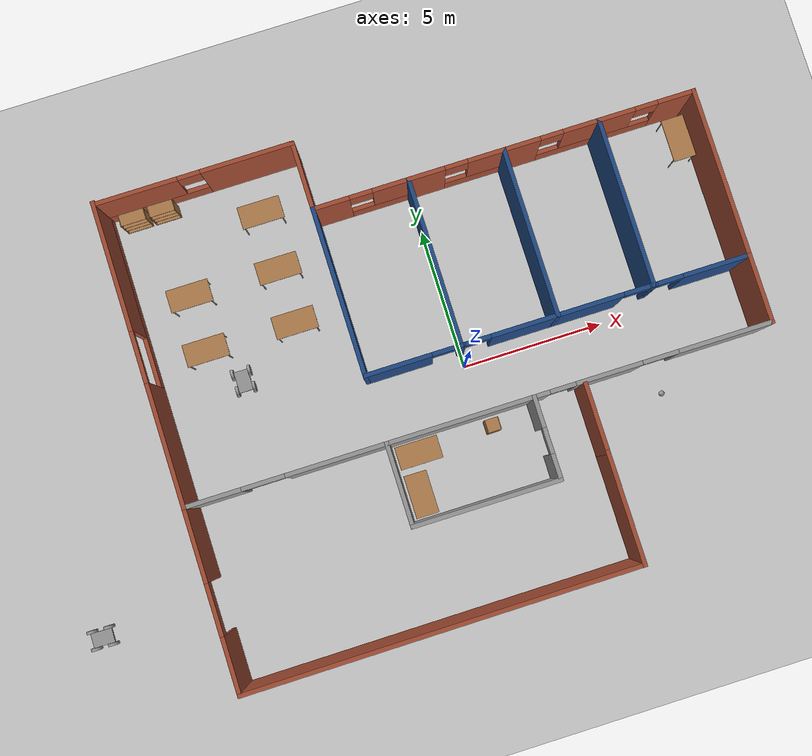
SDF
<sdf version="1.7">
 <world name="default">
  <plugin name="welcome" filename="libwelcome.so"/>
  <light name="sun" type="directional">
   <pose>0 0 10 0 -0 0</pose>
   <diffuse>0.8 0.8 0.8 1</diffuse>
   <specular>0.2 0.2 0.2 1</specular>
   <attenuation>
    <range>1000</range>
    <constant>0.9</constant>
    <linear>0.01</linear>
    <quadratic>0.001</quadratic>
   </attenuation>
   <direction>-0.5 0.1 -0.9</direction>
   <spot><inner_angle>0</inner_angle><outer_angle>0</outer_angle><falloff>0</falloff></spot>
  </light>
  <model name="ground_plane">
   <static>1</static>
   <link name="link">
    <collision name="collision">
     <geometry><plane><normal>0 0 1</normal><size>100 100</size></plane></geometry>
     <surface>
      <contact><collide_bitmask>65535</collide_bitmask></contact>
      <friction><ode><mu>100</mu><mu2>50</mu2></ode></friction>
     </surface>
    </collision>
    <visual name="visual">
     <cast_shadows>0</cast_shadows>
     <geometry><plane><normal>0 0 1</normal><size>100 100</size></plane></geometry>
     <material>
      <script><uri>file://media/materials/scripts/gazebo.material</uri><name>Gazebo/Grey</name></script>
     </material>
    </visual>
   </link>
  </model>
  <gravity>0 0 -9.8</gravity>
  <magnetic_field>6e-06 2.3e-05 -4.2e-05</magnetic_field>
  <atmosphere type="adiabatic"/>
  <physics type="ode">
   <max_step_size>0.001</max_step_size>
   <real_time_factor>1</real_time_factor>
   <real_time_update_rate>1000</real_time_update_rate>
  </physics>
  <scene><ambient>0.4 0.4 0.4 1</ambient><background>0.7 0.7 0.7 1</background><shadows>0</shadows></scene>
  <spherical_coordinates>
   <surface_model>EARTH_WGS84</surface_model>
   <latitude_deg>0</latitude_deg>
   <longitude_deg>0</longitude_deg>
   <elevation>0</elevation>
   <heading_deg>0</heading_deg>
  </spherical_coordinates>
  <model name="Building">
   <pose>-0.15134 0.280793 0 0 -0 0</pose>
   <link name="Wall_10">
    <pose>8.50013 0.225124 0 0 -0 0</pose>
    <visual name="Wall_10_Visual_0">
     <pose>-1.64755 0 1.25 0 -0 0</pose>
     <geometry><box><size>0.204911 0.15 2.5</size></box></geometry>
     <material>
      <script><uri>file://media/materials/scripts/gazebo.material</uri><name>Gazebo/Grey</name></script>
      <ambient>0.12549 0.290196 0.529412 1</ambient>
     </material>
     <meta><layer>0</layer></meta>
    </visual>
    <collision name="Wall_10_Collision_0">
     <geometry><box><size>0.204911 0.15 2.5</size></box></geometry>
     <pose>-1.64755 0 1.25 0 -0 0</pose>
    </collision>
    <visual name="Wall_10_Visual_1">
     <pose>0.552455 0 1.25 0 -0 0</pose>
     <geometry><box><size>2.39509 0.15 2.5</size></box></geometry>
     <material>
      <script><uri>file://media/materials/scripts/gazebo.material</uri><name>Gazebo/Grey</name></script>
      <ambient>0.12549 0.290196 0.529412 1</ambient>
     </material>
     <meta><layer>0</layer></meta>
    </visual>
    <collision name="Wall_10_Collision_1">
     <geometry><box><size>2.39509 0.15 2.5</size></box></geometry>
     <pose>0.552455 0 1.25 0 -0 0</pose>
    </collision>
    <visual name="Wall_10_Visual_2">
     <pose>-1.09509 0 2.25 0 -0 0</pose>
     <geometry><box><size>0.9 0.15 0.5</size></box></geometry>
     <material>
      <script><uri>file://media/materials/scripts/gazebo.material</uri><name>Gazebo/Grey</name></script>
      <ambient>0.12549 0.290196 0.529412 1</ambient>
     </material>
     <meta><layer>0</layer></meta>
    </visual>
    <collision name="Wall_10_Collision_2">
     <geometry><box><size>0.9 0.15 0.5</size></box></geometry>
     <pose>-1.09509 0 2.25 0 -0 0</pose>
    </collision>
   </link>
   <link name="Wall_12">
    <pose>5.15013 0.225124 0 0 -0 3.14159</pose>
    <visual name="Wall_12_Visual_0">
     <pose>-1.64576 0 1.25 0 -0 0</pose>
     <geometry><box><size>0.208483 0.15 2.5</size></box></geometry>
     <material>
      <script><uri>file://media/materials/scripts/gazebo.material</uri><name>Gazebo/Grey</name></script>
      <ambient>0.12549 0.290196 0.529412 1</ambient>
     </material>
     <meta><layer>0</layer></meta>
    </visual>
    <collision name="Wall_12_Collision_0">
     <geometry><box><size>0.208483 0.15 2.5</size></box></geometry>
     <pose>-1.64576 0 1.25 0 -0 0</pose>
    </collision>
    <visual name="Wall_12_Visual_1">
     <pose>0.554241 0 1.25 0 -0 0</pose>
     <geometry><box><size>2.39152 0.15 2.5</size></box></geometry>
     <material>
      <script><uri>file://media/materials/scripts/gazebo.material</uri><name>Gazebo/Grey</name></script>
      <ambient>0.12549 0.290196 0.529412 1</ambient>
     </material>
     <meta><layer>0</layer></meta>
    </visual>
    <collision name="Wall_12_Collision_1">
     <geometry><box><size>2.39152 0.15 2.5</size></box></geometry>
     <pose>0.554241 0 1.25 0 -0 0</pose>
    </collision>
    <visual name="Wall_12_Visual_2">
     <pose>-1.09152 0 2.25 0 -0 0</pose>
     <geometry><box><size>0.9 0.15 0.5</size></box></geometry>
     <material>
      <script><uri>file://media/materials/scripts/gazebo.material</uri><name>Gazebo/Grey</name></script>
      <ambient>0.12549 0.290196 0.529412 1</ambient>
     </material>
     <meta><layer>0</layer></meta>
    </visual>
    <collision name="Wall_12_Collision_2">
     <geometry><box><size>0.9 0.15 0.5</size></box></geometry>
     <pose>-1.09152 0 2.25 0 -0 0</pose>
    </collision>
   </link>
   <link name="Wall_13">
    <collision name="Wall_13_Collision">
     <geometry><box><size>6 0.15 2.5</size></box></geometry>
     <pose>0 0 1.25 0 -0 0</pose>
    </collision>
    <visual name="Wall_13_Visual">
     <pose>0 0 1.25 0 -0 0</pose>
     <geometry><box><size>6 0.15 2.5</size></box></geometry>
     <material>
      <script><uri>file://media/materials/scripts/gazebo.material</uri><name>Gazebo/Grey</name></script>
      <ambient>0.12549 0.290196 0.529412 1</ambient>
     </material>
     <meta><layer>0</layer></meta>
    </visual>
    <pose>3.47512 3.15012 0 0 -0 1.5708</pose>
   </link>
   <link name="Wall_14">
    <pose>5.15013 6.07512 0 0 -0 0</pose>
    <visual name="Wall_14_Visual_0">
     <pose>-1.06914 0 1.25 0 -0 0</pose>
     <geometry><box><size>1.36172 0.15 2.5</size></box></geometry>
     <material>
      <script><uri>file://media/materials/scripts/gazebo.material</uri><name>Gazebo/Bricks</name></script>
      <ambient>0.333333 0.341176 0.32549 1</ambient>
     </material>
     <meta><layer>0</layer></meta>
    </visual>
    <collision name="Wall_14_Collision_0">
     <geometry><box><size>1.36172 0.15 2.5</size></box></geometry>
     <pose>-1.06914 0 1.25 0 -0 0</pose>
    </collision>
    <visual name="Wall_14_Visual_1">
     <pose>0.68086 0 0.35 0 -0 0</pose>
     <geometry><box><size>2.13828 0.15 0.7</size></box></geometry>
     <material>
      <script><uri>file://media/materials/scripts/gazebo.material</uri><name>Gazebo/Bricks</name></script>
      <ambient>0.333333 0.341176 0.32549 1</ambient>
     </material>
     <meta><layer>0</layer></meta>
    </visual>
    <collision name="Wall_14_Collision_1">
     <geometry><box><size>2.13828 0.15 0.7</size></box></geometry>
     <pose>0.68086 0 0.35 0 -0 0</pose>
    </collision>
    <visual name="Wall_14_Visual_2">
     <pose>1.08086 0 1.6 0 -0 0</pose>
     <geometry><box><size>1.33828 0.15 1.8</size></box></geometry>
     <material>
      <script><uri>file://media/materials/scripts/gazebo.material</uri><name>Gazebo/Bricks</name></script>
      <ambient>0.333333 0.341176 0.32549 1</ambient>
     </material>
     <meta><layer>0</layer></meta>
    </visual>
    <collision name="Wall_14_Collision_2">
     <geometry><box><size>1.33828 0.15 1.8</size></box></geometry>
     <pose>1.08086 0 1.6 0 -0 0</pose>
    </collision>
    <visual name="Wall_14_Visual_3">
     <pose>0.01172 0 2.1 0 -0 0</pose>
     <geometry><box><size>0.8 0.15 0.8</size></box></geometry>
     <material>
      <script><uri>file://media/materials/scripts/gazebo.material</uri><name>Gazebo/Bricks</name></script>
      <ambient>0.333333 0.341176 0.32549 1</ambient>
     </material>
     <meta><layer>0</layer></meta>
    </visual>
    <collision name="Wall_14_Collision_3">
     <geometry><box><size>0.8 0.15 0.8</size></box></geometry>
     <pose>0.01172 0 2.1 0 -0 0</pose>
    </collision>
   </link>
   <link name="Wall_16">
    <pose>1.80012 0.225124 0 0 -0 3.14159</pose>
    <visual name="Wall_16_Visual_0">
     <pose>-0.551484 0 1.25 0 -0 0</pose>
     <geometry><box><size>2.39703 0.15 2.5</size></box></geometry>
     <material>
      <script><uri>file://media/materials/scripts/gazebo.material</uri><name>Gazebo/Grey</name></script>
      <ambient>0.12549 0.290196 0.529412 1</ambient>
     </material>
     <meta><layer>0</layer></meta>
    </visual>
    <collision name="Wall_16_Collision_0">
     <geometry><box><size>2.39703 0.15 2.5</size></box></geometry>
     <pose>-0.551484 0 1.25 0 -0 0</pose>
    </collision>
    <visual name="Wall_16_Visual_1">
     <pose>1.64852 0 1.25 0 -0 0</pose>
     <geometry><box><size>0.202968 0.15 2.5</size></box></geometry>
     <material>
      <script><uri>file://media/materials/scripts/gazebo.material</uri><name>Gazebo/Grey</name></script>
      <ambient>0.12549 0.290196 0.529412 1</ambient>
     </material>
     <meta><layer>0</layer></meta>
    </visual>
    <collision name="Wall_16_Collision_1">
     <geometry><box><size>0.202968 0.15 2.5</size></box></geometry>
     <pose>1.64852 0 1.25 0 -0 0</pose>
    </collision>
    <visual name="Wall_16_Visual_2">
     <pose>1.09703 0 2.25 0 -0 0</pose>
     <geometry><box><size>0.9 0.15 0.5</size></box></geometry>
     <material>
      <script><uri>file://media/materials/scripts/gazebo.material</uri><name>Gazebo/Grey</name></script>
      <ambient>0.12549 0.290196 0.529412 1</ambient>
     </material>
     <meta><layer>0</layer></meta>
    </visual>
    <collision name="Wall_16_Collision_2">
     <geometry><box><size>0.9 0.15 0.5</size></box></geometry>
     <pose>1.09703 0 2.25 0 -0 0</pose>
    </collision>
   </link>
   <link name="Wall_17">
    <collision name="Wall_17_Collision">
     <geometry><box><size>6 0.15 2.5</size></box></geometry>
     <pose>0 0 1.25 0 -0 0</pose>
    </collision>
    <visual name="Wall_17_Visual">
     <pose>0 0 1.25 0 -0 0</pose>
     <geometry><box><size>6 0.15 2.5</size></box></geometry>
     <material>
      <script><uri>file://media/materials/scripts/gazebo.material</uri><name>Gazebo/Grey</name></script>
      <ambient>0.12549 0.290196 0.529412 1</ambient>
     </material>
     <meta><layer>0</layer></meta>
    </visual>
    <pose>0.125125 3.15012 0 0 -0 1.5708</pose>
   </link>
   <link name="Wall_18">
    <pose>1.80012 6.07512 0 0 -0 0</pose>
    <visual name="Wall_18_Visual_0">
     <pose>-1.07428 0 1.25 0 -0 0</pose>
     <geometry><box><size>1.35145 0.15 2.5</size></box></geometry>
     <material>
      <script><uri>file://media/materials/scripts/gazebo.material</uri><name>Gazebo/Bricks</name></script>
      <ambient>0.333333 0.341176 0.32549 1</ambient>
     </material>
     <meta><layer>0</layer></meta>
    </visual>
    <collision name="Wall_18_Collision_0">
     <geometry><box><size>1.35145 0.15 2.5</size></box></geometry>
     <pose>-1.07428 0 1.25 0 -0 0</pose>
    </collision>
    <visual name="Wall_18_Visual_1">
     <pose>0.675722 0 0.35 0 -0 0</pose>
     <geometry><box><size>2.14855 0.15 0.7</size></box></geometry>
     <material>
      <script><uri>file://media/materials/scripts/gazebo.material</uri><name>Gazebo/Bricks</name></script>
      <ambient>0.333333 0.341176 0.32549 1</ambient>
     </material>
     <meta><layer>0</layer></meta>
    </visual>
    <collision name="Wall_18_Collision_1">
     <geometry><box><size>2.14855 0.15 0.7</size></box></geometry>
     <pose>0.675722 0 0.35 0 -0 0</pose>
    </collision>
    <visual name="Wall_18_Visual_2">
     <pose>1.07572 0 1.6 0 -0 0</pose>
     <geometry><box><size>1.34855 0.15 1.8</size></box></geometry>
     <material>
      <script><uri>file://media/materials/scripts/gazebo.material</uri><name>Gazebo/Bricks</name></script>
      <ambient>0.333333 0.341176 0.32549 1</ambient>
     </material>
     <meta><layer>0</layer></meta>
    </visual>
    <collision name="Wall_18_Collision_2">
     <geometry><box><size>1.34855 0.15 1.8</size></box></geometry>
     <pose>1.07572 0 1.6 0 -0 0</pose>
    </collision>
    <visual name="Wall_18_Visual_3">
     <pose>0.001445 0 2.1 0 -0 0</pose>
     <geometry><box><size>0.8 0.15 0.8</size></box></geometry>
     <material>
      <script><uri>file://media/materials/scripts/gazebo.material</uri><name>Gazebo/Bricks</name></script>
      <ambient>0.333333 0.341176 0.32549 1</ambient>
     </material>
     <meta><layer>0</layer></meta>
    </visual>
    <collision name="Wall_18_Collision_3">
     <geometry><box><size>0.8 0.15 0.8</size></box></geometry>
     <pose>0.001445 0 2.1 0 -0 0</pose>
    </collision>
   </link>
   <link name="Wall_20">
    <pose>-1.54987 0.225124 0 0 -0 3.14159</pose>
    <visual name="Wall_20_Visual_0">
     <pose>-1.64976 0 1.25 0 -0 0</pose>
     <geometry><box><size>0.200481 0.15 2.5</size></box></geometry>
     <material>
      <script><uri>file://media/materials/scripts/gazebo.material</uri><name>Gazebo/Grey</name></script>
      <ambient>0.12549 0.290196 0.529412 1</ambient>
     </material>
     <meta><layer>0</layer></meta>
    </visual>
    <collision name="Wall_20_Collision_0">
     <geometry><box><size>0.200481 0.15 2.5</size></box></geometry>
     <pose>-1.64976 0 1.25 0 -0 0</pose>
    </collision>
    <visual name="Wall_20_Visual_1">
     <pose>0.550241 0 1.25 0 -0 0</pose>
     <geometry><box><size>2.39952 0.15 2.5</size></box></geometry>
     <material>
      <script><uri>file://media/materials/scripts/gazebo.material</uri><name>Gazebo/Grey</name></script>
      <ambient>0.12549 0.290196 0.529412 1</ambient>
     </material>
     <meta><layer>0</layer></meta>
    </visual>
    <collision name="Wall_20_Collision_1">
     <geometry><box><size>2.39952 0.15 2.5</size></box></geometry>
     <pose>0.550241 0 1.25 0 -0 0</pose>
    </collision>
    <visual name="Wall_20_Visual_2">
     <pose>-1.09952 0 2.25 0 -0 0</pose>
     <geometry><box><size>0.9 0.15 0.5</size></box></geometry>
     <material>
      <script><uri>file://media/materials/scripts/gazebo.material</uri><name>Gazebo/Grey</name></script>
      <ambient>0.12549 0.290196 0.529412 1</ambient>
     </material>
     <meta><layer>0</layer></meta>
    </visual>
    <collision name="Wall_20_Collision_2">
     <geometry><box><size>0.9 0.15 0.5</size></box></geometry>
     <pose>-1.09952 0 2.25 0 -0 0</pose>
    </collision>
   </link>
   <link name="Wall_21">
    <collision name="Wall_21_Collision">
     <geometry><box><size>6 0.15 2.5</size></box></geometry>
     <pose>0 0 1.25 0 -0 0</pose>
    </collision>
    <visual name="Wall_21_Visual">
     <pose>0 0 1.25 0 -0 0</pose>
     <geometry><box><size>6 0.15 2.5</size></box></geometry>
     <material>
      <script><uri>file://media/materials/scripts/gazebo.material</uri><name>Gazebo/Grey</name></script>
      <ambient>0.12549 0.290196 0.529412 1</ambient>
     </material>
     <meta><layer>0</layer></meta>
    </visual>
    <pose>-3.22488 3.15012 0 0 -0 1.5708</pose>
   </link>
   <link name="Wall_22">
    <pose>-1.54987 6.07512 0 0 -0 0</pose>
    <visual name="Wall_22_Visual_0">
     <pose>-1.07723 0 1.25 0 -0 0</pose>
     <geometry><box><size>1.34554 0.15 2.5</size></box></geometry>
     <material>
      <script><uri>file://media/materials/scripts/gazebo.material</uri><name>Gazebo/Bricks</name></script>
      <ambient>0.333333 0.341176 0.32549 1</ambient>
     </material>
     <meta><layer>0</layer></meta>
    </visual>
    <collision name="Wall_22_Collision_0">
     <geometry><box><size>1.34554 0.15 2.5</size></box></geometry>
     <pose>-1.07723 0 1.25 0 -0 0</pose>
    </collision>
    <visual name="Wall_22_Visual_1">
     <pose>0.672768 0 0.35 0 -0 0</pose>
     <geometry><box><size>2.15446 0.15 0.7</size></box></geometry>
     <material>
      <script><uri>file://media/materials/scripts/gazebo.material</uri><name>Gazebo/Bricks</name></script>
      <ambient>0.333333 0.341176 0.32549 1</ambient>
     </material>
     <meta><layer>0</layer></meta>
    </visual>
    <collision name="Wall_22_Collision_1">
     <geometry><box><size>2.15446 0.15 0.7</size></box></geometry>
     <pose>0.672768 0 0.35 0 -0 0</pose>
    </collision>
    <visual name="Wall_22_Visual_2">
     <pose>1.07277 0 1.6 0 -0 0</pose>
     <geometry><box><size>1.35446 0.15 1.8</size></box></geometry>
     <material>
      <script><uri>file://media/materials/scripts/gazebo.material</uri><name>Gazebo/Bricks</name></script>
      <ambient>0.333333 0.341176 0.32549 1</ambient>
     </material>
     <meta><layer>0</layer></meta>
    </visual>
    <collision name="Wall_22_Collision_2">
     <geometry><box><size>1.35446 0.15 1.8</size></box></geometry>
     <pose>1.07277 0 1.6 0 -0 0</pose>
    </collision>
    <visual name="Wall_22_Visual_3">
     <pose>-0.004464 0 2.1 0 -0 0</pose>
     <geometry><box><size>0.8 0.15 0.8</size></box></geometry>
     <material>
      <script><uri>file://media/materials/scripts/gazebo.material</uri><name>Gazebo/Bricks</name></script>
      <ambient>0.333333 0.341176 0.32549 1</ambient>
     </material>
     <meta><layer>0</layer></meta>
    </visual>
    <collision name="Wall_22_Collision_3">
     <geometry><box><size>0.8 0.15 0.8</size></box></geometry>
     <pose>-0.004464 0 2.1 0 -0 0</pose>
    </collision>
   </link>
   <link name="Wall_24">
    <collision name="Wall_24_Collision">
     <geometry><box><size>2.5 0.15 2.5</size></box></geometry>
     <pose>0 0 1.25 0 -0 0</pose>
    </collision>
    <visual name="Wall_24_Visual">
     <pose>0 0 1.25 0 -0 0</pose>
     <geometry><box><size>2.5 0.15 2.5</size></box></geometry>
     <material>
      <script><uri>file://media/materials/scripts/gazebo.material</uri><name>Gazebo/Bricks</name></script>
      <ambient>1 1 1 1</ambient>
     </material>
     <meta><layer>0</layer></meta>
    </visual>
    <pose>-3.22488 7.25012 0 0 -0 1.5708</pose>
   </link>
   <link name="Wall_25">
    <pose>-6.64987 8.42512 0 0 -0 3.14159</pose>
    <visual name="Wall_25_Visual_0">
     <pose>-1.84714 0 1.25 0 -0 0</pose>
     <geometry><box><size>3.30572 0.15 2.5</size></box></geometry>
     <material>
      <script><uri>file://media/materials/scripts/gazebo.material</uri><name>Gazebo/Bricks</name></script>
      <ambient>0.333333 0.341176 0.32549 1</ambient>
     </material>
     <meta><layer>0</layer></meta>
    </visual>
    <collision name="Wall_25_Collision_0">
     <geometry><box><size>3.30572 0.15 2.5</size></box></geometry>
     <pose>-1.84714 0 1.25 0 -0 0</pose>
    </collision>
    <visual name="Wall_25_Visual_1">
     <pose>1.65286 0 0.35 0 -0 0</pose>
     <geometry><box><size>3.69428 0.15 0.7</size></box></geometry>
     <material>
      <script><uri>file://media/materials/scripts/gazebo.material</uri><name>Gazebo/Bricks</name></script>
      <ambient>0.333333 0.341176 0.32549 1</ambient>
     </material>
     <meta><layer>0</layer></meta>
    </visual>
    <collision name="Wall_25_Collision_1">
     <geometry><box><size>3.69428 0.15 0.7</size></box></geometry>
     <pose>1.65286 0 0.35 0 -0 0</pose>
    </collision>
    <visual name="Wall_25_Visual_2">
     <pose>2.05286 0 1.6 0 -0 0</pose>
     <geometry><box><size>2.89428 0.15 1.8</size></box></geometry>
     <material>
      <script><uri>file://media/materials/scripts/gazebo.material</uri><name>Gazebo/Bricks</name></script>
      <ambient>0.333333 0.341176 0.32549 1</ambient>
     </material>
     <meta><layer>0</layer></meta>
    </visual>
    <collision name="Wall_25_Collision_2">
     <geometry><box><size>2.89428 0.15 1.8</size></box></geometry>
     <pose>2.05286 0 1.6 0 -0 0</pose>
    </collision>
    <visual name="Wall_25_Visual_3">
     <pose>0.205716 0 2.1 0 -0 0</pose>
     <geometry><box><size>0.8 0.15 0.8</size></box></geometry>
     <material>
      <script><uri>file://media/materials/scripts/gazebo.material</uri><name>Gazebo/Bricks</name></script>
      <ambient>0.333333 0.341176 0.32549 1</ambient>
     </material>
     <meta><layer>0</layer></meta>
    </visual>
    <collision name="Wall_25_Collision_3">
     <geometry><box><size>0.8 0.15 0.8</size></box></geometry>
     <pose>0.205716 0 2.1 0 -0 0</pose>
    </collision>
   </link>
   <link name="Wall_40">
    <pose>0.000125 -2.12488 0 0 -0 3.14159</pose>
    <visual name="Wall_40_Visual_0">
     <pose>-8.57984 0 1.25 0 -0 0</pose>
     <geometry><box><size>3.34032 0.15 2.5</size></box></geometry>
     <material>
      <script><uri>file://media/materials/scripts/gazebo.material</uri><name>Gazebo/Grey</name></script>
      <ambient>0.533333 0.541176 0.521569 1</ambient>
     </material>
     <meta><layer>0</layer></meta>
    </visual>
    <collision name="Wall_40_Collision_0">
     <geometry><box><size>3.34032 0.15 2.5</size></box></geometry>
     <pose>-8.57984 0 1.25 0 -0 0</pose>
    </collision>
    <visual name="Wall_40_Visual_1">
     <pose>-4.49832 0 1.25 0 -0 0</pose>
     <geometry><box><size>2.32272 0.15 2.5</size></box></geometry>
     <material>
      <script><uri>file://media/materials/scripts/gazebo.material</uri><name>Gazebo/Grey</name></script>
      <ambient>0.533333 0.541176 0.521569 1</ambient>
     </material>
     <meta><layer>0</layer></meta>
    </visual>
    <collision name="Wall_40_Collision_1">
     <geometry><box><size>2.32272 0.15 2.5</size></box></geometry>
     <pose>-4.49832 0 1.25 0 -0 0</pose>
    </collision>
    <visual name="Wall_40_Visual_2">
     <pose>2.13723 0 1.25 0 -0 0</pose>
     <geometry><box><size>9.14837 0.15 2.5</size></box></geometry>
     <material>
      <script><uri>file://media/materials/scripts/gazebo.material</uri><name>Gazebo/Grey</name></script>
      <ambient>0.533333 0.541176 0.521569 1</ambient>
     </material>
     <meta><layer>0</layer></meta>
    </visual>
    <collision name="Wall_40_Collision_2">
     <geometry><box><size>9.14837 0.15 2.5</size></box></geometry>
     <pose>2.13723 0 1.25 0 -0 0</pose>
    </collision>
    <visual name="Wall_40_Visual_3">
     <pose>9.23071 0 1.25 0 -0 0</pose>
     <geometry><box><size>2.03859 0.15 2.5</size></box></geometry>
     <material>
      <script><uri>file://media/materials/scripts/gazebo.material</uri><name>Gazebo/Grey</name></script>
      <ambient>0.533333 0.541176 0.521569 1</ambient>
     </material>
     <meta><layer>0</layer></meta>
    </visual>
    <collision name="Wall_40_Collision_3">
     <geometry><box><size>2.03859 0.15 2.5</size></box></geometry>
     <pose>9.23071 0 1.25 0 -0 0</pose>
    </collision>
    <visual name="Wall_40_Visual_4">
     <pose>-6.28468 0 2.25 0 -0 0</pose>
     <geometry><box><size>1.25 0.15 0.5</size></box></geometry>
     <material>
      <script><uri>file://media/materials/scripts/gazebo.material</uri><name>Gazebo/Grey</name></script>
      <ambient>0.533333 0.541176 0.521569 1</ambient>
     </material>
     <meta><layer>0</layer></meta>
    </visual>
    <collision name="Wall_40_Collision_4">
     <geometry><box><size>1.25 0.15 0.5</size></box></geometry>
     <pose>-6.28468 0 2.25 0 -0 0</pose>
    </collision>
    <visual name="Wall_40_Visual_5">
     <pose>-2.88696 0 2.25 0 -0 0</pose>
     <geometry><box><size>0.9 0.15 0.5</size></box></geometry>
     <material>
      <script><uri>file://media/materials/scripts/gazebo.material</uri><name>Gazebo/Grey</name></script>
      <ambient>0.533333 0.541176 0.521569 1</ambient>
     </material>
     <meta><layer>0</layer></meta>
    </visual>
    <collision name="Wall_40_Collision_5">
     <geometry><box><size>0.9 0.15 0.5</size></box></geometry>
     <pose>-2.88696 0 2.25 0 -0 0</pose>
    </collision>
    <visual name="Wall_40_Visual_6">
     <pose>7.46141 0 2.25 0 -0 0</pose>
     <geometry><box><size>1.5 0.15 0.5</size></box></geometry>
     <material>
      <script><uri>file://media/materials/scripts/gazebo.material</uri><name>Gazebo/Grey</name></script>
      <ambient>0.533333 0.541176 0.521569 1</ambient>
     </material>
     <meta><layer>0</layer></meta>
    </visual>
    <collision name="Wall_40_Collision_6">
     <geometry><box><size>1.5 0.15 0.5</size></box></geometry>
     <pose>7.46141 0 2.25 0 -0 0</pose>
    </collision>
   </link>
   <link name="Wall_41">
    <pose>-10.1749 3.17512 0 0 -0 1.5708</pose>
    <visual name="Wall_41_Visual_0">
     <pose>-3.19655 0 1.25 0 -0 0</pose>
     <geometry><box><size>4.3569 0.15 2.5</size></box></geometry>
     <material>
      <script><uri>file://media/materials/scripts/gazebo.material</uri><name>Gazebo/Bricks</name></script>
      <ambient>0.333333 0.341176 0.32549 1</ambient>
     </material>
     <meta><layer>0</layer></meta>
    </visual>
    <collision name="Wall_41_Collision_0">
     <geometry><box><size>4.3569 0.15 2.5</size></box></geometry>
     <pose>-3.19655 0 1.25 0 -0 0</pose>
    </collision>
    <visual name="Wall_41_Visual_1">
     <pose>2.17845 0 0.25 0 -0 0</pose>
     <geometry><box><size>6.3931 0.15 0.5</size></box></geometry>
     <material>
      <script><uri>file://media/materials/scripts/gazebo.material</uri><name>Gazebo/Bricks</name></script>
      <ambient>0.333333 0.341176 0.32549 1</ambient>
     </material>
     <meta><layer>0</layer></meta>
    </visual>
    <collision name="Wall_41_Collision_1">
     <geometry><box><size>6.3931 0.15 0.5</size></box></geometry>
     <pose>2.17845 0 0.25 0 -0 0</pose>
    </collision>
    <visual name="Wall_41_Visual_2">
     <pose>3.07845 0 1.5 0 -0 0</pose>
     <geometry><box><size>4.5931 0.15 2</size></box></geometry>
     <material>
      <script><uri>file://media/materials/scripts/gazebo.material</uri><name>Gazebo/Bricks</name></script>
      <ambient>0.333333 0.341176 0.32549 1</ambient>
     </material>
     <meta><layer>0</layer></meta>
    </visual>
    <collision name="Wall_41_Collision_2">
     <geometry><box><size>4.5931 0.15 2</size></box></geometry>
     <pose>3.07845 0 1.5 0 -0 0</pose>
    </collision>
    <visual name="Wall_41_Visual_3">
     <pose>-0.118096 0 2.4 0 -0 0</pose>
     <geometry><box><size>1.8 0.15 0.2</size></box></geometry>
     <material>
      <script><uri>file://media/materials/scripts/gazebo.material</uri><name>Gazebo/Bricks</name></script>
      <ambient>0.333333 0.341176 0.32549 1</ambient>
     </material>
     <meta><layer>0</layer></meta>
    </visual>
    <collision name="Wall_41_Collision_3">
     <geometry><box><size>1.8 0.15 0.2</size></box></geometry>
     <pose>-0.118096 0 2.4 0 -0 0</pose>
    </collision>
   </link>
   <link name="Wall_43">
    <collision name="Wall_43_Collision">
     <geometry><box><size>2.5 0.15 2.5</size></box></geometry>
     <pose>0 0 1.25 0 -0 0</pose>
    </collision>
    <visual name="Wall_43_Visual">
     <pose>0 0 1.25 0 -0 0</pose>
     <geometry><box><size>2.5 0.15 2.5</size></box></geometry>
     <material>
      <script><uri>file://media/materials/scripts/gazebo.material</uri><name>Gazebo/Bricks</name></script>
      <ambient>1 1 1 1</ambient>
     </material>
     <meta><layer>0</layer></meta>
    </visual>
    <pose>3.6418 -3.40395 0 0 -0 -1.5708</pose>
   </link>
   <link name="Wall_44">
    <collision name="Wall_44_Collision">
     <geometry><box><size>4 0.15 2.5</size></box></geometry>
     <pose>0 0 1.25 0 -0 0</pose>
    </collision>
    <visual name="Wall_44_Visual">
     <pose>0 0 1.25 0 -0 0</pose>
     <geometry><box><size>4 0.15 2.5</size></box></geometry>
     <material>
      <script><uri>file://media/materials/scripts/gazebo.material</uri><name>Gazebo/Bricks</name></script>
      <ambient>1 1 1 1</ambient>
     </material>
     <meta><layer>0</layer></meta>
    </visual>
    <pose>3.6418 -6.50395 0 0 -0 -1.5708</pose>
   </link>
   <link name="Wall_46">
    <pose>1.89213 -3.55088 0 0 -0 -1.5708</pose>
    <visual name="Wall_46_Visual_0">
     <pose>-0.932706 0 1.25 0 -0 0</pose>
     <geometry><box><size>1.13459 0.15 2.5</size></box></geometry>
     <material>
      <script><uri>file://media/materials/scripts/gazebo.material</uri><name>Gazebo/Grey</name></script>
      <ambient>0.533333 0.541176 0.521569 1</ambient>
     </material>
     <meta><layer>0</layer></meta>
    </visual>
    <collision name="Wall_46_Collision_0">
     <geometry><box><size>1.13459 0.15 2.5</size></box></geometry>
     <pose>-0.932706 0 1.25 0 -0 0</pose>
    </collision>
    <visual name="Wall_46_Visual_1">
     <pose>1.01729 0 1.25 0 -0 0</pose>
     <geometry><box><size>0.965411 0.15 2.5</size></box></geometry>
     <material>
      <script><uri>file://media/materials/scripts/gazebo.material</uri><name>Gazebo/Grey</name></script>
      <ambient>0.533333 0.541176 0.521569 1</ambient>
     </material>
     <meta><layer>0</layer></meta>
    </visual>
    <collision name="Wall_46_Collision_1">
     <geometry><box><size>0.965411 0.15 2.5</size></box></geometry>
     <pose>1.01729 0 1.25 0 -0 0</pose>
    </collision>
    <visual name="Wall_46_Visual_2">
     <pose>0.084589 0 2.25 0 -0 0</pose>
     <geometry><box><size>0.9 0.15 0.5</size></box></geometry>
     <material>
      <script><uri>file://media/materials/scripts/gazebo.material</uri><name>Gazebo/Grey</name></script>
      <ambient>0.533333 0.541176 0.521569 1</ambient>
     </material>
     <meta><layer>0</layer></meta>
    </visual>
    <collision name="Wall_46_Collision_2">
     <geometry><box><size>0.9 0.15 0.5</size></box></geometry>
     <pose>0.084589 0 2.25 0 -0 0</pose>
    </collision>
   </link>
   <link name="Wall_47">
    <collision name="Wall_47_Collision">
     <geometry><box><size>5.25 0.15 2.5</size></box></geometry>
     <pose>0 0 1.25 0 -0 0</pose>
    </collision>
    <visual name="Wall_47_Visual">
     <pose>0 0 1.25 0 -0 0</pose>
     <geometry><box><size>5.25 0.15 2.5</size></box></geometry>
     <material>
      <script><uri>file://media/materials/scripts/gazebo.material</uri><name>Gazebo/Grey</name></script>
      <ambient>0.533333 0.541176 0.521569 1</ambient>
     </material>
     <meta><layer>0</layer></meta>
    </visual>
    <pose>-0.657821 -4.97595 0 0 -0 -3.14156</pose>
   </link>
   <link name="Wall_48">
    <collision name="Wall_48_Collision">
     <geometry><box><size>3 0.15 2.5</size></box></geometry>
     <pose>0 0 1.25 0 -0 0</pose>
    </collision>
    <visual name="Wall_48_Visual">
     <pose>0 0 1.25 0 -0 0</pose>
     <geometry><box><size>3 0.15 2.5</size></box></geometry>
     <material>
      <script><uri>file://media/materials/scripts/gazebo.material</uri><name>Gazebo/Grey</name></script>
      <ambient>0.533333 0.541176 0.521569 1</ambient>
     </material>
     <meta><layer>0</layer></meta>
    </visual>
    <pose>-3.20777 -3.55104 0 0 -0 1.5708</pose>
   </link>
   <link name="Wall_5">
    <collision name="Wall_5_Collision">
     <geometry><box><size>2.5 0.15 2.5</size></box></geometry>
     <pose>0 0 1.25 0 -0 0</pose>
    </collision>
    <visual name="Wall_5_Visual">
     <pose>0 0 1.25 0 -0 0</pose>
     <geometry><box><size>2.5 0.15 2.5</size></box></geometry>
     <material>
      <script><uri>file://media/materials/scripts/gazebo.material</uri><name>Gazebo/Bricks</name></script>
      <ambient>0.333333 0.341176 0.32549 1</ambient>
     </material>
     <meta><layer>0</layer></meta>
    </visual>
    <pose>10.1751 -0.949876 0 0 -0 1.5708</pose>
   </link>
   <link name="Wall_52">
    <pose>-10.1749 -5.29988 0 0 -0 -1.5708</pose>
    <visual name="Wall_52_Visual_0">
     <pose>-1.92266 0 1.25 0 -0 0</pose>
     <geometry><box><size>2.65469 0.15 2.5</size></box></geometry>
     <material>
      <script><uri>file://media/materials/scripts/gazebo.material</uri><name>Gazebo/Bricks</name></script>
      <ambient>1 1 1 1</ambient>
     </material>
     <meta><layer>0</layer></meta>
    </visual>
    <collision name="Wall_52_Collision_0">
     <geometry><box><size>2.65469 0.15 2.5</size></box></geometry>
     <pose>-1.92266 0 1.25 0 -0 0</pose>
    </collision>
    <visual name="Wall_52_Visual_1">
     <pose>2.22734 0 1.25 0 -0 0</pose>
     <geometry><box><size>2.04531 0.15 2.5</size></box></geometry>
     <material>
      <script><uri>file://media/materials/scripts/gazebo.material</uri><name>Gazebo/Bricks</name></script>
      <ambient>1 1 1 1</ambient>
     </material>
     <meta><layer>0</layer></meta>
    </visual>
    <collision name="Wall_52_Collision_1">
     <geometry><box><size>2.04531 0.15 2.5</size></box></geometry>
     <pose>2.22734 0 1.25 0 -0 0</pose>
    </collision>
    <visual name="Wall_52_Visual_2">
     <pose>0.304685 0 2.25 0 -0 0</pose>
     <geometry><box><size>1.8 0.15 0.5</size></box></geometry>
     <material>
      <script><uri>file://media/materials/scripts/gazebo.material</uri><name>Gazebo/Bricks</name></script>
      <ambient>1 1 1 1</ambient>
     </material>
     <meta><layer>0</layer></meta>
    </visual>
    <collision name="Wall_52_Collision_2">
     <geometry><box><size>1.8 0.15 0.5</size></box></geometry>
     <pose>0.304685 0 2.25 0 -0 0</pose>
    </collision>
   </link>
   <link name="Wall_54">
    <collision name="Wall_54_Collision">
     <geometry><box><size>13.9667 0.15 2.5</size></box></geometry>
     <pose>0 0 1.25 0 -0 0</pose>
    </collision>
    <visual name="Wall_54_Visual">
     <pose>0 0 1.25 0 -0 0</pose>
     <geometry><box><size>13.9667 0.15 2.5</size></box></geometry>
     <material>
      <script><uri>file://media/materials/scripts/gazebo.material</uri><name>Gazebo/Bricks</name></script>
      <ambient>1 1 1 1</ambient>
     </material>
     <meta><layer>0</layer></meta>
    </visual>
    <pose>-3.26654 -8.45191 0 0 -0 -3.13827</pose>
   </link>
   <link name="Wall_6">
    <collision name="Wall_6_Collision">
     <geometry><box><size>6 0.15 2.5</size></box></geometry>
     <pose>0 0 1.25 0 -0 0</pose>
    </collision>
    <visual name="Wall_6_Visual">
     <pose>0 0 1.25 0 -0 0</pose>
     <geometry><box><size>6 0.15 2.5</size></box></geometry>
     <material>
      <script><uri>file://media/materials/scripts/gazebo.material</uri><name>Gazebo/Bricks</name></script>
      <ambient>0.333333 0.341176 0.32549 1</ambient>
     </material>
     <meta><layer>0</layer></meta>
    </visual>
    <pose>10.1751 3.15012 0 0 -0 1.5708</pose>
   </link>
   <link name="Wall_8">
    <pose>8.50013 6.07512 0 0 -0 3.14159</pose>
    <visual name="Wall_8_Visual_0">
     <pose>-1.07616 0 1.25 0 -0 0</pose>
     <geometry><box><size>1.34768 0.15 2.5</size></box></geometry>
     <material>
      <script><uri>file://media/materials/scripts/gazebo.material</uri><name>Gazebo/Bricks</name></script>
      <ambient>0.333333 0.341176 0.32549 1</ambient>
     </material>
     <meta><layer>0</layer></meta>
    </visual>
    <collision name="Wall_8_Collision_0">
     <geometry><box><size>1.34768 0.15 2.5</size></box></geometry>
     <pose>-1.07616 0 1.25 0 -0 0</pose>
    </collision>
    <visual name="Wall_8_Visual_1">
     <pose>0.673839 0 0.35 0 -0 0</pose>
     <geometry><box><size>2.15232 0.15 0.7</size></box></geometry>
     <material>
      <script><uri>file://media/materials/scripts/gazebo.material</uri><name>Gazebo/Bricks</name></script>
      <ambient>0.333333 0.341176 0.32549 1</ambient>
     </material>
     <meta><layer>0</layer></meta>
    </visual>
    <collision name="Wall_8_Collision_1">
     <geometry><box><size>2.15232 0.15 0.7</size></box></geometry>
     <pose>0.673839 0 0.35 0 -0 0</pose>
    </collision>
    <visual name="Wall_8_Visual_2">
     <pose>1.07384 0 1.6 0 -0 0</pose>
     <geometry><box><size>1.35232 0.15 1.8</size></box></geometry>
     <material>
      <script><uri>file://media/materials/scripts/gazebo.material</uri><name>Gazebo/Bricks</name></script>
      <ambient>0.333333 0.341176 0.32549 1</ambient>
     </material>
     <meta><layer>0</layer></meta>
    </visual>
    <collision name="Wall_8_Collision_2">
     <geometry><box><size>1.35232 0.15 1.8</size></box></geometry>
     <pose>1.07384 0 1.6 0 -0 0</pose>
    </collision>
    <visual name="Wall_8_Visual_3">
     <pose>-0.002322 0 2.1 0 -0 0</pose>
     <geometry><box><size>0.8 0.15 0.8</size></box></geometry>
     <material>
      <script><uri>file://media/materials/scripts/gazebo.material</uri><name>Gazebo/Bricks</name></script>
      <ambient>0.333333 0.341176 0.32549 1</ambient>
     </material>
     <meta><layer>0</layer></meta>
    </visual>
    <collision name="Wall_8_Collision_3">
     <geometry><box><size>0.8 0.15 0.8</size></box></geometry>
     <pose>-0.002322 0 2.1 0 -0 0</pose>
    </collision>
   </link>
   <link name="Wall_9">
    <collision name="Wall_9_Collision">
     <geometry><box><size>6 0.15 2.5</size></box></geometry>
     <pose>0 0 1.25 0 -0 0</pose>
    </collision>
    <visual name="Wall_9_Visual">
     <pose>0 0 1.25 0 -0 0</pose>
     <geometry><box><size>6 0.15 2.5</size></box></geometry>
     <material>
      <script><uri>file://media/materials/scripts/gazebo.material</uri><name>Gazebo/Grey</name></script>
      <ambient>0.12549 0.290196 0.529412 1</ambient>
     </material>
     <meta><layer>0</layer></meta>
    </visual>
    <pose>6.82512 3.15012 0 0 -0 -1.5708</pose>
   </link>
   <static>1</static>
  </model>
  <model name="bookshelf">
   <static>1</static>
   <link name="link">
    <inertial><mass>1</mass></inertial>
    <collision name="back">
     <pose>0 0.005 0.6 0 -0 0</pose>
     <geometry><box><size>0.9 0.01 1.2</size></box></geometry>
    </collision>
    <visual name="visual1">
     <pose>0 0.005 0.6 0 -0 0</pose>
     <geometry><box><size>0.9 0.01 1.2</size></box></geometry>
     <material>
      <script><uri>file://media/materials/scripts/gazebo.material</uri><name>Gazebo/Wood</name></script>
     </material>
    </visual>
    <collision name="left_side">
     <pose>0.45 -0.195 0.6 0 -0 0</pose>
     <geometry><box><size>0.02 0.4 1.2</size></box></geometry>
    </collision>
    <visual name="visual2">
     <pose>0.45 -0.195 0.6 0 -0 0</pose>
     <geometry><box><size>0.02 0.4 1.2</size></box></geometry>
     <material>
      <script><uri>file://media/materials/scripts/gazebo.material</uri><name>Gazebo/Wood</name></script>
     </material>
    </visual>
    <collision name="right_side">
     <pose>-0.45 -0.195 0.6 0 -0 0</pose>
     <geometry><box><size>0.02 0.4 1.2</size></box></geometry>
    </collision>
    <visual name="visual3">
     <pose>-0.45 -0.195 0.6 0 -0 0</pose>
     <geometry><box><size>0.02 0.4 1.2</size></box></geometry>
     <material>
      <script><uri>file://media/materials/scripts/gazebo.material</uri><name>Gazebo/Wood</name></script>
     </material>
    </visual>
    <collision name="bottom">
     <pose>0 -0.195 0.03 0 -0 0</pose>
     <geometry><box><size>0.88 0.4 0.06</size></box></geometry>
    </collision>
    <visual name="visual4">
     <pose>0 -0.195 0.03 0 -0 0</pose>
     <geometry><box><size>0.88 0.4 0.06</size></box></geometry>
     <material>
      <script><uri>file://media/materials/scripts/gazebo.material</uri><name>Gazebo/Wood</name></script>
     </material>
    </visual>
    <collision name="top">
     <pose>0 -0.195 1.19 0 -0 0</pose>
     <geometry><box><size>0.88 0.4 0.02</size></box></geometry>
    </collision>
    <visual name="visual5">
     <pose>0 -0.195 1.19 0 -0 0</pose>
     <geometry><box><size>0.88 0.4 0.02</size></box></geometry>
     <material>
      <script><uri>file://media/materials/scripts/gazebo.material</uri><name>Gazebo/Wood</name></script>
     </material>
    </visual>
    <collision name="low_shelf">
     <pose>0 -0.195 0.43 0 -0 0</pose>
     <geometry><box><size>0.88 0.4 0.02</size></box></geometry>
    </collision>
    <visual name="visual6">
     <pose>0 -0.195 0.43 0 -0 0</pose>
     <geometry><box><size>0.88 0.4 0.02</size></box></geometry>
     <material>
      <script><uri>file://media/materials/scripts/gazebo.material</uri><name>Gazebo/Wood</name></script>
     </material>
    </visual>
    <collision name="high_shelf">
     <pose>0 -0.195 0.8 0 -0 0</pose>
     <geometry><box><size>0.88 0.4 0.02</size></box></geometry>
    </collision>
    <visual name="visual7">
     <pose>0 -0.195 0.8 0 -0 0</pose>
     <geometry><box><size>0.88 0.4 0.02</size></box></geometry>
     <material>
      <script><uri>file://media/materials/scripts/gazebo.material</uri><name>Gazebo/Wood</name></script>
     </material>
    </visual>
   </link>
   <pose>-9.4279 8.4763 0 0 -0 0</pose>
  </model>
  <model name="bookshelf_0">
   <static>1</static>
   <link name="link">
    <inertial><mass>1</mass></inertial>
    <collision name="back">
     <pose>0 0.005 0.6 0 -0 0</pose>
     <geometry><box><size>0.9 0.01 1.2</size></box></geometry>
    </collision>
    <visual name="visual1">
     <pose>0 0.005 0.6 0 -0 0</pose>
     <geometry><box><size>0.9 0.01 1.2</size></box></geometry>
     <material>
      <script><uri>file://media/materials/scripts/gazebo.material</uri><name>Gazebo/Wood</name></script>
     </material>
    </visual>
    <collision name="left_side">
     <pose>0.45 -0.195 0.6 0 -0 0</pose>
     <geometry><box><size>0.02 0.4 1.2</size></box></geometry>
    </collision>
    <visual name="visual2">
     <pose>0.45 -0.195 0.6 0 -0 0</pose>
     <geometry><box><size>0.02 0.4 1.2</size></box></geometry>
     <material>
      <script><uri>file://media/materials/scripts/gazebo.material</uri><name>Gazebo/Wood</name></script>
     </material>
    </visual>
    <collision name="right_side">
     <pose>-0.45 -0.195 0.6 0 -0 0</pose>
     <geometry><box><size>0.02 0.4 1.2</size></box></geometry>
    </collision>
    <visual name="visual3">
     <pose>-0.45 -0.195 0.6 0 -0 0</pose>
     <geometry><box><size>0.02 0.4 1.2</size></box></geometry>
     <material>
      <script><uri>file://media/materials/scripts/gazebo.material</uri><name>Gazebo/Wood</name></script>
     </material>
    </visual>
    <collision name="bottom">
     <pose>0 -0.195 0.03 0 -0 0</pose>
     <geometry><box><size>0.88 0.4 0.06</size></box></geometry>
    </collision>
    <visual name="visual4">
     <pose>0 -0.195 0.03 0 -0 0</pose>
     <geometry><box><size>0.88 0.4 0.06</size></box></geometry>
     <material>
      <script><uri>file://media/materials/scripts/gazebo.material</uri><name>Gazebo/Wood</name></script>
     </material>
    </visual>
    <collision name="top">
     <pose>0 -0.195 1.19 0 -0 0</pose>
     <geometry><box><size>0.88 0.4 0.02</size></box></geometry>
    </collision>
    <visual name="visual5">
     <pose>0 -0.195 1.19 0 -0 0</pose>
     <geometry><box><size>0.88 0.4 0.02</size></box></geometry>
     <material>
      <script><uri>file://media/materials/scripts/gazebo.material</uri><name>Gazebo/Wood</name></script>
     </material>
    </visual>
    <collision name="low_shelf">
     <pose>0 -0.195 0.43 0 -0 0</pose>
     <geometry><box><size>0.88 0.4 0.02</size></box></geometry>
    </collision>
    <visual name="visual6">
     <pose>0 -0.195 0.43 0 -0 0</pose>
     <geometry><box><size>0.88 0.4 0.02</size></box></geometry>
     <material>
      <script><uri>file://media/materials/scripts/gazebo.material</uri><name>Gazebo/Wood</name></script>
     </material>
    </visual>
    <collision name="high_shelf">
     <pose>0 -0.195 0.8 0 -0 0</pose>
     <geometry><box><size>0.88 0.4 0.02</size></box></geometry>
    </collision>
    <visual name="visual7">
     <pose>0 -0.195 0.8 0 -0 0</pose>
     <geometry><box><size>0.88 0.4 0.02</size></box></geometry>
     <material>
      <script><uri>file://media/materials/scripts/gazebo.material</uri><name>Gazebo/Wood</name></script>
     </material>
    </visual>
   </link>
   <pose>-8.39294 8.4763 0 0 -0 0</pose>
  </model>
  <model name="table">
   <static>1</static>
   <link name="link">
    <collision name="surface">
     <pose>0 0 1 0 -0 0</pose>
     <geometry><box><size>1.5 0.8 0.03</size></box></geometry>
     <surface><friction><ode><mu>0.6</mu><mu2>0.6</mu2></ode></friction></surface>
    </collision>
    <visual name="visual1">
     <pose>0 0 1 0 -0 0</pose>
     <geometry><box><size>1.5 0.8 0.03</size></box></geometry>
     <material>
      <script><uri>file://media/materials/scripts/gazebo.material</uri><name>Gazebo/Wood</name></script>
     </material>
    </visual>
    <collision name="front_left_leg">
     <pose>0.68 0.38 0.5 0 -0 0</pose>
     <geometry><cylinder><radius>0.02</radius><length>1</length></cylinder></geometry>
    </collision>
    <visual name="front_left_leg">
     <pose>0.68 0.38 0.5 0 -0 0</pose>
     <geometry><cylinder><radius>0.02</radius><length>1</length></cylinder></geometry>
     <material>
      <script><uri>file://media/materials/scripts/gazebo.material</uri><name>Gazebo/Grey</name></script>
     </material>
    </visual>
    <collision name="front_right_leg">
     <pose>0.68 -0.38 0.5 0 -0 0</pose>
     <geometry><cylinder><radius>0.02</radius><length>1</length></cylinder></geometry>
    </collision>
    <visual name="front_right_leg">
     <pose>0.68 -0.38 0.5 0 -0 0</pose>
     <geometry><cylinder><radius>0.02</radius><length>1</length></cylinder></geometry>
     <material>
      <script><uri>file://media/materials/scripts/gazebo.material</uri><name>Gazebo/Grey</name></script>
     </material>
    </visual>
    <collision name="back_right_leg">
     <pose>-0.68 -0.38 0.5 0 -0 0</pose>
     <geometry><cylinder><radius>0.02</radius><length>1</length></cylinder></geometry>
    </collision>
    <visual name="back_right_leg">
     <pose>-0.68 -0.38 0.5 0 -0 0</pose>
     <geometry><cylinder><radius>0.02</radius><length>1</length></cylinder></geometry>
     <material>
      <script><uri>file://media/materials/scripts/gazebo.material</uri><name>Gazebo/Grey</name></script>
     </material>
    </visual>
    <collision name="back_left_leg">
     <pose>-0.68 0.38 0.5 0 -0 0</pose>
     <geometry><cylinder><radius>0.02</radius><length>1</length></cylinder></geometry>
    </collision>
    <visual name="back_left_leg">
     <pose>-0.68 0.38 0.5 0 -0 0</pose>
     <geometry><cylinder><radius>0.02</radius><length>1</length></cylinder></geometry>
     <material>
      <script><uri>file://media/materials/scripts/gazebo.material</uri><name>Gazebo/Grey</name></script>
     </material>
    </visual>
   </link>
   <pose>-5.16056 7.15737 0 0 -0 0</pose>
  </model>
  <model name="table_clone">
   <static>1</static>
   <link name="link">
    <collision name="surface">
     <pose>0 0 1 0 -0 0</pose>
     <geometry><box><size>1.5 0.8 0.03</size></box></geometry>
     <surface><friction><ode><mu>0.6</mu><mu2>0.6</mu2></ode></friction></surface>
    </collision>
    <visual name="visual1">
     <pose>0 0 1 0 -0 0</pose>
     <geometry><box><size>1.5 0.8 0.03</size></box></geometry>
     <material>
      <script><uri>file://media/materials/scripts/gazebo.material</uri><name>Gazebo/Wood</name></script>
     </material>
    </visual>
    <collision name="front_left_leg">
     <pose>0.68 0.38 0.5 0 -0 0</pose>
     <geometry><cylinder><radius>0.02</radius><length>1</length></cylinder></geometry>
    </collision>
    <visual name="front_left_leg">
     <pose>0.68 0.38 0.5 0 -0 0</pose>
     <geometry><cylinder><radius>0.02</radius><length>1</length></cylinder></geometry>
     <material>
      <script><uri>file://media/materials/scripts/gazebo.material</uri><name>Gazebo/Grey</name></script>
     </material>
    </visual>
    <collision name="front_right_leg">
     <pose>0.68 -0.38 0.5 0 -0 0</pose>
     <geometry><cylinder><radius>0.02</radius><length>1</length></cylinder></geometry>
    </collision>
    <visual name="front_right_leg">
     <pose>0.68 -0.38 0.5 0 -0 0</pose>
     <geometry><cylinder><radius>0.02</radius><length>1</length></cylinder></geometry>
     <material>
      <script><uri>file://media/materials/scripts/gazebo.material</uri><name>Gazebo/Grey</name></script>
     </material>
    </visual>
    <collision name="back_right_leg">
     <pose>-0.68 -0.38 0.5 0 -0 0</pose>
     <geometry><cylinder><radius>0.02</radius><length>1</length></cylinder></geometry>
    </collision>
    <visual name="back_right_leg">
     <pose>-0.68 -0.38 0.5 0 -0 0</pose>
     <geometry><cylinder><radius>0.02</radius><length>1</length></cylinder></geometry>
     <material>
      <script><uri>file://media/materials/scripts/gazebo.material</uri><name>Gazebo/Grey</name></script>
     </material>
    </visual>
    <collision name="back_left_leg">
     <pose>-0.68 0.38 0.5 0 -0 0</pose>
     <geometry><cylinder><radius>0.02</radius><length>1</length></cylinder></geometry>
    </collision>
    <visual name="back_left_leg">
     <pose>-0.68 0.38 0.5 0 -0 0</pose>
     <geometry><cylinder><radius>0.02</radius><length>1</length></cylinder></geometry>
     <material>
      <script><uri>file://media/materials/scripts/gazebo.material</uri><name>Gazebo/Grey</name></script>
     </material>
    </visual>
   </link>
   <pose>-5.16056 5.1087 0 0 -0 0</pose>
  </model>
  <model name="table_clone_0">
   <static>1</static>
   <link name="link">
    <collision name="surface">
     <pose>0 0 1 0 -0 0</pose>
     <geometry><box><size>1.5 0.8 0.03</size></box></geometry>
     <surface><friction><ode><mu>0.6</mu><mu2>0.6</mu2></ode></friction></surface>
    </collision>
    <visual name="visual1">
     <pose>0 0 1 0 -0 0</pose>
     <geometry><box><size>1.5 0.8 0.03</size></box></geometry>
     <material>
      <script><uri>file://media/materials/scripts/gazebo.material</uri><name>Gazebo/Wood</name></script>
     </material>
    </visual>
    <collision name="front_left_leg">
     <pose>0.68 0.38 0.5 0 -0 0</pose>
     <geometry><cylinder><radius>0.02</radius><length>1</length></cylinder></geometry>
    </collision>
    <visual name="front_left_leg">
     <pose>0.68 0.38 0.5 0 -0 0</pose>
     <geometry><cylinder><radius>0.02</radius><length>1</length></cylinder></geometry>
     <material>
      <script><uri>file://media/materials/scripts/gazebo.material</uri><name>Gazebo/Grey</name></script>
     </material>
    </visual>
    <collision name="front_right_leg">
     <pose>0.68 -0.38 0.5 0 -0 0</pose>
     <geometry><cylinder><radius>0.02</radius><length>1</length></cylinder></geometry>
    </collision>
    <visual name="front_right_leg">
     <pose>0.68 -0.38 0.5 0 -0 0</pose>
     <geometry><cylinder><radius>0.02</radius><length>1</length></cylinder></geometry>
     <material>
      <script><uri>file://media/materials/scripts/gazebo.material</uri><name>Gazebo/Grey</name></script>
     </material>
    </visual>
    <collision name="back_right_leg">
     <pose>-0.68 -0.38 0.5 0 -0 0</pose>
     <geometry><cylinder><radius>0.02</radius><length>1</length></cylinder></geometry>
    </collision>
    <visual name="back_right_leg">
     <pose>-0.68 -0.38 0.5 0 -0 0</pose>
     <geometry><cylinder><radius>0.02</radius><length>1</length></cylinder></geometry>
     <material>
      <script><uri>file://media/materials/scripts/gazebo.material</uri><name>Gazebo/Grey</name></script>
     </material>
    </visual>
    <collision name="back_left_leg">
     <pose>-0.68 0.38 0.5 0 -0 0</pose>
     <geometry><cylinder><radius>0.02</radius><length>1</length></cylinder></geometry>
    </collision>
    <visual name="back_left_leg">
     <pose>-0.68 0.38 0.5 0 -0 0</pose>
     <geometry><cylinder><radius>0.02</radius><length>1</length></cylinder></geometry>
     <material>
      <script><uri>file://media/materials/scripts/gazebo.material</uri><name>Gazebo/Grey</name></script>
     </material>
    </visual>
   </link>
   <pose>-5.16056 3.13783 0 0 -0 0</pose>
  </model>
  <model name="table_clone_1">
   <static>1</static>
   <link name="link">
    <collision name="surface">
     <pose>0 0 1 0 -0 0</pose>
     <geometry><box><size>1.5 0.8 0.03</size></box></geometry>
     <surface><friction><ode><mu>0.6</mu><mu2>0.6</mu2></ode></friction></surface>
    </collision>
    <visual name="visual1">
     <pose>0 0 1 0 -0 0</pose>
     <geometry><box><size>1.5 0.8 0.03</size></box></geometry>
     <material>
      <script><uri>file://media/materials/scripts/gazebo.material</uri><name>Gazebo/Wood</name></script>
     </material>
    </visual>
    <collision name="front_left_leg">
     <pose>0.68 0.38 0.5 0 -0 0</pose>
     <geometry><cylinder><radius>0.02</radius><length>1</length></cylinder></geometry>
    </collision>
    <visual name="front_left_leg">
     <pose>0.68 0.38 0.5 0 -0 0</pose>
     <geometry><cylinder><radius>0.02</radius><length>1</length></cylinder></geometry>
     <material>
      <script><uri>file://media/materials/scripts/gazebo.material</uri><name>Gazebo/Grey</name></script>
     </material>
    </visual>
    <collision name="front_right_leg">
     <pose>0.68 -0.38 0.5 0 -0 0</pose>
     <geometry><cylinder><radius>0.02</radius><length>1</length></cylinder></geometry>
    </collision>
    <visual name="front_right_leg">
     <pose>0.68 -0.38 0.5 0 -0 0</pose>
     <geometry><cylinder><radius>0.02</radius><length>1</length></cylinder></geometry>
     <material>
      <script><uri>file://media/materials/scripts/gazebo.material</uri><name>Gazebo/Grey</name></script>
     </material>
    </visual>
    <collision name="back_right_leg">
     <pose>-0.68 -0.38 0.5 0 -0 0</pose>
     <geometry><cylinder><radius>0.02</radius><length>1</length></cylinder></geometry>
    </collision>
    <visual name="back_right_leg">
     <pose>-0.68 -0.38 0.5 0 -0 0</pose>
     <geometry><cylinder><radius>0.02</radius><length>1</length></cylinder></geometry>
     <material>
      <script><uri>file://media/materials/scripts/gazebo.material</uri><name>Gazebo/Grey</name></script>
     </material>
    </visual>
    <collision name="back_left_leg">
     <pose>-0.68 0.38 0.5 0 -0 0</pose>
     <geometry><cylinder><radius>0.02</radius><length>1</length></cylinder></geometry>
    </collision>
    <visual name="back_left_leg">
     <pose>-0.68 0.38 0.5 0 -0 0</pose>
     <geometry><cylinder><radius>0.02</radius><length>1</length></cylinder></geometry>
     <material>
      <script><uri>file://media/materials/scripts/gazebo.material</uri><name>Gazebo/Grey</name></script>
     </material>
    </visual>
   </link>
   <pose>-8.35026 5.1087 0 0 -0 0</pose>
  </model>
  <model name="table_clone_2">
   <static>1</static>
   <link name="link">
    <collision name="surface">
     <pose>0 0 1 0 -0 0</pose>
     <geometry><box><size>1.5 0.8 0.03</size></box></geometry>
     <surface><friction><ode><mu>0.6</mu><mu2>0.6</mu2></ode></friction></surface>
    </collision>
    <visual name="visual1">
     <pose>0 0 1 0 -0 0</pose>
     <geometry><box><size>1.5 0.8 0.03</size></box></geometry>
     <material>
      <script><uri>file://media/materials/scripts/gazebo.material</uri><name>Gazebo/Wood</name></script>
     </material>
    </visual>
    <collision name="front_left_leg">
     <pose>0.68 0.38 0.5 0 -0 0</pose>
     <geometry><cylinder><radius>0.02</radius><length>1</length></cylinder></geometry>
    </collision>
    <visual name="front_left_leg">
     <pose>0.68 0.38 0.5 0 -0 0</pose>
     <geometry><cylinder><radius>0.02</radius><length>1</length></cylinder></geometry>
     <material>
      <script><uri>file://media/materials/scripts/gazebo.material</uri><name>Gazebo/Grey</name></script>
     </material>
    </visual>
    <collision name="front_right_leg">
     <pose>0.68 -0.38 0.5 0 -0 0</pose>
     <geometry><cylinder><radius>0.02</radius><length>1</length></cylinder></geometry>
    </collision>
    <visual name="front_right_leg">
     <pose>0.68 -0.38 0.5 0 -0 0</pose>
     <geometry><cylinder><radius>0.02</radius><length>1</length></cylinder></geometry>
     <material>
      <script><uri>file://media/materials/scripts/gazebo.material</uri><name>Gazebo/Grey</name></script>
     </material>
    </visual>
    <collision name="back_right_leg">
     <pose>-0.68 -0.38 0.5 0 -0 0</pose>
     <geometry><cylinder><radius>0.02</radius><length>1</length></cylinder></geometry>
    </collision>
    <visual name="back_right_leg">
     <pose>-0.68 -0.38 0.5 0 -0 0</pose>
     <geometry><cylinder><radius>0.02</radius><length>1</length></cylinder></geometry>
     <material>
      <script><uri>file://media/materials/scripts/gazebo.material</uri><name>Gazebo/Grey</name></script>
     </material>
    </visual>
    <collision name="back_left_leg">
     <pose>-0.68 0.38 0.5 0 -0 0</pose>
     <geometry><cylinder><radius>0.02</radius><length>1</length></cylinder></geometry>
    </collision>
    <visual name="back_left_leg">
     <pose>-0.68 0.38 0.5 0 -0 0</pose>
     <geometry><cylinder><radius>0.02</radius><length>1</length></cylinder></geometry>
     <material>
      <script><uri>file://media/materials/scripts/gazebo.material</uri><name>Gazebo/Grey</name></script>
     </material>
    </visual>
   </link>
   <pose>-8.35026 3.13783 0 0 -0 0</pose>
  </model>
  <model name="table_0">
   <static>1</static>
   <link name="link">
    <collision name="surface">
     <pose>0 0 1 0 -0 0</pose>
     <geometry><box><size>1.5 0.8 0.03</size></box></geometry>
     <surface><friction><ode><mu>0.6</mu><mu2>0.6</mu2></ode></friction></surface>
    </collision>
    <visual name="visual1">
     <pose>0 0 1 0 -0 0</pose>
     <geometry><box><size>1.5 0.8 0.03</size></box></geometry>
     <material>
      <script><uri>file://media/materials/scripts/gazebo.material</uri><name>Gazebo/Wood</name></script>
     </material>
    </visual>
    <collision name="front_left_leg">
     <pose>0.68 0.38 0.5 0 -0 0</pose>
     <geometry><cylinder><radius>0.02</radius><length>1</length></cylinder></geometry>
    </collision>
    <visual name="front_left_leg">
     <pose>0.68 0.38 0.5 0 -0 0</pose>
     <geometry><cylinder><radius>0.02</radius><length>1</length></cylinder></geometry>
     <material>
      <script><uri>file://media/materials/scripts/gazebo.material</uri><name>Gazebo/Grey</name></script>
     </material>
    </visual>
    <collision name="front_right_leg">
     <pose>0.68 -0.38 0.5 0 -0 0</pose>
     <geometry><cylinder><radius>0.02</radius><length>1</length></cylinder></geometry>
    </collision>
    <visual name="front_right_leg">
     <pose>0.68 -0.38 0.5 0 -0 0</pose>
     <geometry><cylinder><radius>0.02</radius><length>1</length></cylinder></geometry>
     <material>
      <script><uri>file://media/materials/scripts/gazebo.material</uri><name>Gazebo/Grey</name></script>
     </material>
    </visual>
    <collision name="back_right_leg">
     <pose>-0.68 -0.38 0.5 0 -0 0</pose>
     <geometry><cylinder><radius>0.02</radius><length>1</length></cylinder></geometry>
    </collision>
    <visual name="back_right_leg">
     <pose>-0.68 -0.38 0.5 0 -0 0</pose>
     <geometry><cylinder><radius>0.02</radius><length>1</length></cylinder></geometry>
     <material>
      <script><uri>file://media/materials/scripts/gazebo.material</uri><name>Gazebo/Grey</name></script>
     </material>
    </visual>
    <collision name="back_left_leg">
     <pose>-0.68 0.38 0.5 0 -0 0</pose>
     <geometry><cylinder><radius>0.02</radius><length>1</length></cylinder></geometry>
    </collision>
    <visual name="back_left_leg">
     <pose>-0.68 0.38 0.5 0 -0 0</pose>
     <geometry><cylinder><radius>0.02</radius><length>1</length></cylinder></geometry>
     <material>
      <script><uri>file://media/materials/scripts/gazebo.material</uri><name>Gazebo/Grey</name></script>
     </material>
    </visual>
   </link>
   <pose>-2.43902 -2.40672 0 0 -0 0</pose>
  </model>
  <model name="table_1">
   <static>1</static>
   <link name="link">
    <collision name="surface">
     <pose>0 0 1 0 -0 0</pose>
     <geometry><box><size>1.5 0.8 0.03</size></box></geometry>
     <surface><friction><ode><mu>0.6</mu><mu2>0.6</mu2></ode></friction></surface>
    </collision>
    <visual name="visual1">
     <pose>0 0 1 0 -0 0</pose>
     <geometry><box><size>1.5 0.8 0.03</size></box></geometry>
     <material>
      <script><uri>file://media/materials/scripts/gazebo.material</uri><name>Gazebo/Wood</name></script>
     </material>
    </visual>
    <collision name="front_left_leg">
     <pose>0.68 0.38 0.5 0 -0 0</pose>
     <geometry><cylinder><radius>0.02</radius><length>1</length></cylinder></geometry>
    </collision>
    <visual name="front_left_leg">
     <pose>0.68 0.38 0.5 0 -0 0</pose>
     <geometry><cylinder><radius>0.02</radius><length>1</length></cylinder></geometry>
     <material>
      <script><uri>file://media/materials/scripts/gazebo.material</uri><name>Gazebo/Grey</name></script>
     </material>
    </visual>
    <collision name="front_right_leg">
     <pose>0.68 -0.38 0.5 0 -0 0</pose>
     <geometry><cylinder><radius>0.02</radius><length>1</length></cylinder></geometry>
    </collision>
    <visual name="front_right_leg">
     <pose>0.68 -0.38 0.5 0 -0 0</pose>
     <geometry><cylinder><radius>0.02</radius><length>1</length></cylinder></geometry>
     <material>
      <script><uri>file://media/materials/scripts/gazebo.material</uri><name>Gazebo/Grey</name></script>
     </material>
    </visual>
    <collision name="back_right_leg">
     <pose>-0.68 -0.38 0.5 0 -0 0</pose>
     <geometry><cylinder><radius>0.02</radius><length>1</length></cylinder></geometry>
    </collision>
    <visual name="back_right_leg">
     <pose>-0.68 -0.38 0.5 0 -0 0</pose>
     <geometry><cylinder><radius>0.02</radius><length>1</length></cylinder></geometry>
     <material>
      <script><uri>file://media/materials/scripts/gazebo.material</uri><name>Gazebo/Grey</name></script>
     </material>
    </visual>
    <collision name="back_left_leg">
     <pose>-0.68 0.38 0.5 0 -0 0</pose>
     <geometry><cylinder><radius>0.02</radius><length>1</length></cylinder></geometry>
    </collision>
    <visual name="back_left_leg">
     <pose>-0.68 0.38 0.5 0 -0 0</pose>
     <geometry><cylinder><radius>0.02</radius><length>1</length></cylinder></geometry>
     <material>
      <script><uri>file://media/materials/scripts/gazebo.material</uri><name>Gazebo/Grey</name></script>
     </material>
    </visual>
   </link>
   <pose>-2.78167 -3.78506 0 0 -0 1.57</pose>
  </model>
  <model name="cabinet">
   <static>1</static>
   <link name="cabinet_bottom_plate">
    <inertial>
     <pose>0 0 -1 0 -0 0</pose>
     <inertia><ixx>2.05</ixx><ixy>0</ixy><ixz>0</ixz><iyy>2.05</iyy><iyz>0</iyz><izz>2.05</izz></inertia>
     <mass>25</mass>
    </inertial>
    <collision name="cabinet_bottom_plate_geom">
     <pose>0 0 0.01 0 -0 0</pose>
     <geometry><box><size>0.45 0.45 0.02</size></box></geometry>
    </collision>
    <visual name="cabinet_bottom_plate_geom_visual">
     <pose>0 0 0.01 0 -0 0</pose>
     <geometry><box><size>0.45 0.45 0.02</size></box></geometry>
     <material>
      <script><uri>file://media/materials/scripts/gazebo.material</uri><name>Gazebo/Wood</name></script>
     </material>
    </visual>
    <collision name="cabinet_bottom_plate_geom_cabinet_back_plate">
     <pose>0.235 0 0.51 0 -0 0</pose>
     <geometry><box><size>0.02 0.45 1.02</size></box></geometry>
    </collision>
    <visual name="cabinet_bottom_plate_geom_cabinet_back_plate_visual">
     <pose>0.235 0 0.51 0 -0 0</pose>
     <geometry><box><size>0.02 0.45 1.02</size></box></geometry>
     <material>
      <script><uri>file://media/materials/scripts/gazebo.material</uri><name>Gazebo/Wood</name></script>
     </material>
    </visual>
    <collision name="cabinet_bottom_plate_geom_cabinet_left_plate">
     <pose>0 0.235 0.51 0 -0 0</pose>
     <geometry><box><size>0.45 0.02 1.02</size></box></geometry>
    </collision>
    <visual name="cabinet_bottom_plate_geom_cabinet_left_plate_visual">
     <pose>0 0.235 0.51 0 -0 0</pose>
     <geometry><box><size>0.45 0.02 1.02</size></box></geometry>
     <material>
      <script><uri>file://media/materials/scripts/gazebo.material</uri><name>Gazebo/Wood</name></script>
     </material>
    </visual>
    <collision name="cabinet_bottom_plate_geom_cabinet_middle_plate">
     <pose>0 0 0.51 0 -0 0</pose>
     <geometry><box><size>0.45 0.45 0.02</size></box></geometry>
    </collision>
    <visual name="cabinet_bottom_plate_geom_cabinet_middle_plate_visual">
     <pose>0 0 0.51 0 -0 0</pose>
     <geometry><box><size>0.45 0.45 0.02</size></box></geometry>
     <material>
      <script><uri>file://media/materials/scripts/gazebo.material</uri><name>Gazebo/Wood</name></script>
     </material>
    </visual>
    <collision name="cabinet_bottom_plate_geom_cabinet_right_plate">
     <pose>0 -0.235 0.51 0 -0 0</pose>
     <geometry><box><size>0.45 0.02 1.02</size></box></geometry>
    </collision>
    <visual name="cabinet_bottom_plate_geom_cabinet_right_plate_visual">
     <pose>0 -0.235 0.51 0 -0 0</pose>
     <geometry><box><size>0.45 0.02 1.02</size></box></geometry>
     <material>
      <script><uri>file://media/materials/scripts/gazebo.material</uri><name>Gazebo/Wood</name></script>
     </material>
    </visual>
    <collision name="cabinet_bottom_plate_geom_cabinet_top_plate">
     <pose>0 0 1.01 0 -0 0</pose>
     <geometry><box><size>0.45 0.45 0.02</size></box></geometry>
    </collision>
    <visual name="cabinet_bottom_plate_geom_cabinet_top_plate_visual">
     <pose>0 0 1.01 0 -0 0</pose>
     <geometry><box><size>0.45 0.45 0.02</size></box></geometry>
     <material>
      <script><uri>file://media/materials/scripts/gazebo.material</uri><name>Gazebo/Wood</name></script>
     </material>
    </visual>
   </link>
   <pose>0.259392 -2.26466 0 0 0 -1.57</pose>
  </model>
  <model name="table_2">
   <static>1</static>
   <link name="link">
    <collision name="surface">
     <pose>0 0 1 0 -0 0</pose>
     <geometry><box><size>1.5 0.8 0.03</size></box></geometry>
     <surface><friction><ode><mu>0.6</mu><mu2>0.6</mu2></ode></friction></surface>
    </collision>
    <visual name="visual1">
     <pose>0 0 1 0 -0 0</pose>
     <geometry><box><size>1.5 0.8 0.03</size></box></geometry>
     <material>
      <script><uri>file://media/materials/scripts/gazebo.material</uri><name>Gazebo/Wood</name></script>
     </material>
    </visual>
    <collision name="front_left_leg">
     <pose>0.68 0.38 0.5 0 -0 0</pose>
     <geometry><cylinder><radius>0.02</radius><length>1</length></cylinder></geometry>
    </collision>
    <visual name="front_left_leg">
     <pose>0.68 0.38 0.5 0 -0 0</pose>
     <geometry><cylinder><radius>0.02</radius><length>1</length></cylinder></geometry>
     <material>
      <script><uri>file://media/materials/scripts/gazebo.material</uri><name>Gazebo/Grey</name></script>
     </material>
    </visual>
    <collision name="front_right_leg">
     <pose>0.68 -0.38 0.5 0 -0 0</pose>
     <geometry><cylinder><radius>0.02</radius><length>1</length></cylinder></geometry>
    </collision>
    <visual name="front_right_leg">
     <pose>0.68 -0.38 0.5 0 -0 0</pose>
     <geometry><cylinder><radius>0.02</radius><length>1</length></cylinder></geometry>
     <material>
      <script><uri>file://media/materials/scripts/gazebo.material</uri><name>Gazebo/Grey</name></script>
     </material>
    </visual>
    <collision name="back_right_leg">
     <pose>-0.68 -0.38 0.5 0 -0 0</pose>
     <geometry><cylinder><radius>0.02</radius><length>1</length></cylinder></geometry>
    </collision>
    <visual name="back_right_leg">
     <pose>-0.68 -0.38 0.5 0 -0 0</pose>
     <geometry><cylinder><radius>0.02</radius><length>1</length></cylinder></geometry>
     <material>
      <script><uri>file://media/materials/scripts/gazebo.material</uri><name>Gazebo/Grey</name></script>
     </material>
    </visual>
    <collision name="back_left_leg">
     <pose>-0.68 0.38 0.5 0 -0 0</pose>
     <geometry><cylinder><radius>0.02</radius><length>1</length></cylinder></geometry>
    </collision>
    <visual name="back_left_leg">
     <pose>-0.68 0.38 0.5 0 -0 0</pose>
     <geometry><cylinder><radius>0.02</radius><length>1</length></cylinder></geometry>
     <material>
      <script><uri>file://media/materials/scripts/gazebo.material</uri><name>Gazebo/Grey</name></script>
     </material>
    </visual>
   </link>
   <pose>9.45767 5.29063 0 0 -0 1.57</pose>
  </model>
  <model name="four_wheeled_robot">
   <link name="link_0">
    <inertial>
     <mass>1</mass>
     <inertia>
      <ixx>0.166667</ixx>
      <ixy>0</ixy>
      <ixz>0</ixz>
      <iyy>0.166667</iyy>
      <iyz>0</iyz>
      <izz>0.166667</izz>
     </inertia>
    </inertial>
    <pose>-0.085901 0 -0.120032 0 -0 0</pose>
    <visual name="visual">
     <geometry><box><size>0.75 0.5 0.1</size></box></geometry>
     <material>
      <lighting>1</lighting>
      <script><uri>file://media/materials/scripts/gazebo.material</uri><name>Gazebo/Grey</name></script>
      <shader type="pixel"><normal_map>__default__</normal_map></shader>
      <ambient>0.3 0.3 0.3 1</ambient>
      <diffuse>0.7 0.7 0.7 1</diffuse>
      <specular>0.01 0.01 0.01 1</specular>
      <emissive>0 0 0 1</emissive>
     </material>
    </visual>
    <collision name="collision">
     <geometry><box><size>0.75 0.5 0.1</size></box></geometry>
     <surface>
      <friction>
       <ode><mu>1</mu><mu2>1</mu2><fdir1>0 0 0</fdir1><slip1>0</slip1><slip2>0</slip2></ode>
       <torsional>
        <coefficient>1</coefficient>
        <patch_radius>0</patch_radius>
        <surface_radius>0</surface_radius>
        <use_patch_radius>1</use_patch_radius>
        <ode><slip>0</slip></ode>
       </torsional>
      </friction>
      <bounce><restitution_coefficient>0</restitution_coefficient><threshold>1e+06</threshold></bounce>
      <contact>
       <collide_without_contact>0</collide_without_contact>
       <collide_without_contact_bitmask>1</collide_without_contact_bitmask>
       <collide_bitmask>1</collide_bitmask>
       <ode>
        <soft_cfm>0</soft_cfm>
        <soft_erp>0.2</soft_erp>
        <kp>1e+13</kp>
        <kd>1</kd>
        <max_vel>0.01</max_vel>
        <min_depth>0</min_depth>
       </ode>
       <bullet>
        <split_impulse>1</split_impulse>
        <split_impulse_penetration_threshold>-0.01</split_impulse_penetration_threshold>
        <soft_cfm>0</soft_cfm>
        <soft_erp>0.2</soft_erp>
        <kp>1e+13</kp>
        <kd>1</kd>
       </bullet>
      </contact>
     </surface>
    </collision>
   </link>
   <link name="link_1">
    <inertial>
     <mass>1</mass>
     <inertia><ixx>0.145833</ixx><ixy>0</ixy><ixz>0</ixz><iyy>0.145833</iyy><iyz>0</iyz><izz>0.125</izz></inertia>
    </inertial>
    <pose>-0.385901 0.300159 -0.120032 -1.57 0 0</pose>
    <visual name="visual">
     <geometry><cylinder><radius>0.2</radius><length>0.1</length></cylinder></geometry>
     <material>
      <lighting>1</lighting>
      <script><uri>file://media/materials/scripts/gazebo.material</uri><name>Gazebo/Grey</name></script>
      <shader type="pixel"><normal_map>__default__</normal_map></shader>
      <ambient>0.3 0.3 0.3 1</ambient>
      <diffuse>0.7 0.7 0.7 1</diffuse>
      <specular>0.01 0.01 0.01 1</specular>
      <emissive>0 0 0 1</emissive>
     </material>
    </visual>
    <collision name="collision">
     <geometry><cylinder><radius>0.2</radius><length>0.1</length></cylinder></geometry>
     <surface>
      <friction>
       <ode><mu>1</mu><mu2>1</mu2><fdir1>0 0 0</fdir1><slip1>0</slip1><slip2>0</slip2></ode>
       <torsional>
        <coefficient>1</coefficient>
        <patch_radius>0</patch_radius>
        <surface_radius>0</surface_radius>
        <use_patch_radius>1</use_patch_radius>
        <ode><slip>0</slip></ode>
       </torsional>
      </friction>
      <bounce><restitution_coefficient>0</restitution_coefficient><threshold>1e+06</threshold></bounce>
      <contact>
       <collide_without_contact>0</collide_without_contact>
       <collide_without_contact_bitmask>1</collide_without_contact_bitmask>
       <collide_bitmask>1</collide_bitmask>
       <ode>
        <soft_cfm>0</soft_cfm>
        <soft_erp>0.2</soft_erp>
        <kp>1e+13</kp>
        <kd>1</kd>
        <max_vel>0.01</max_vel>
        <min_depth>0</min_depth>
       </ode>
       <bullet>
        <split_impulse>1</split_impulse>
        <split_impulse_penetration_threshold>-0.01</split_impulse_penetration_threshold>
        <soft_cfm>0</soft_cfm>
        <soft_erp>0.2</soft_erp>
        <kp>1e+13</kp>
        <kd>1</kd>
       </bullet>
      </contact>
     </surface>
    </collision>
   </link>
   <link name="link_1_clone">
    <inertial>
     <mass>1</mass>
     <inertia><ixx>0.145833</ixx><ixy>0</ixy><ixz>0</ixz><iyy>0.145833</iyy><iyz>0</iyz><izz>0.125</izz></inertia>
    </inertial>
    <pose>0.214099 0.300159 -0.120032 -1.57 0 0</pose>
    <visual name="visual">
     <geometry><cylinder><radius>0.2</radius><length>0.1</length></cylinder></geometry>
     <material>
      <lighting>1</lighting>
      <script><uri>file://media/materials/scripts/gazebo.material</uri><name>Gazebo/Grey</name></script>
      <shader type="pixel"><normal_map>__default__</normal_map></shader>
      <ambient>0.3 0.3 0.3 1</ambient>
      <diffuse>0.7 0.7 0.7 1</diffuse>
      <specular>0.01 0.01 0.01 1</specular>
      <emissive>0 0 0 1</emissive>
     </material>
    </visual>
    <collision name="collision">
     <geometry><cylinder><radius>0.2</radius><length>0.1</length></cylinder></geometry>
     <surface>
      <friction>
       <ode><mu>1</mu><mu2>1</mu2><fdir1>0 0 0</fdir1><slip1>0</slip1><slip2>0</slip2></ode>
       <torsional>
        <coefficient>1</coefficient>
        <patch_radius>0</patch_radius>
        <surface_radius>0</surface_radius>
        <use_patch_radius>1</use_patch_radius>
        <ode><slip>0</slip></ode>
       </torsional>
      </friction>
      <bounce><restitution_coefficient>0</restitution_coefficient><threshold>1e+06</threshold></bounce>
      <contact>
       <collide_without_contact>0</collide_without_contact>
       <collide_without_contact_bitmask>1</collide_without_contact_bitmask>
       <collide_bitmask>1</collide_bitmask>
       <ode>
        <soft_cfm>0</soft_cfm>
        <soft_erp>0.2</soft_erp>
        <kp>1e+13</kp>
        <kd>1</kd>
        <max_vel>0.01</max_vel>
        <min_depth>0</min_depth>
       </ode>
       <bullet>
        <split_impulse>1</split_impulse>
        <split_impulse_penetration_threshold>-0.01</split_impulse_penetration_threshold>
        <soft_cfm>0</soft_cfm>
        <soft_erp>0.2</soft_erp>
        <kp>1e+13</kp>
        <kd>1</kd>
       </bullet>
      </contact>
     </surface>
    </collision>
   </link>
   <link name="link_1_clone_0">
    <inertial>
     <mass>1</mass>
     <inertia><ixx>0.145833</ixx><ixy>0</ixy><ixz>0</ixz><iyy>0.145833</iyy><iyz>0</iyz><izz>0.125</izz></inertia>
    </inertial>
    <pose>0.214099 -0.300159 -0.120032 -1.57 0 0</pose>
    <visual name="visual">
     <geometry><cylinder><radius>0.2</radius><length>0.1</length></cylinder></geometry>
     <material>
      <lighting>1</lighting>
      <script><uri>file://media/materials/scripts/gazebo.material</uri><name>Gazebo/Grey</name></script>
      <shader type="pixel"><normal_map>__default__</normal_map></shader>
      <ambient>0.3 0.3 0.3 1</ambient>
      <diffuse>0.7 0.7 0.7 1</diffuse>
      <specular>0.01 0.01 0.01 1</specular>
      <emissive>0 0 0 1</emissive>
     </material>
    </visual>
    <collision name="collision">
     <geometry><cylinder><radius>0.2</radius><length>0.1</length></cylinder></geometry>
     <surface>
      <friction>
       <ode><mu>1</mu><mu2>1</mu2><fdir1>0 0 0</fdir1><slip1>0</slip1><slip2>0</slip2></ode>
       <torsional>
        <coefficient>1</coefficient>
        <patch_radius>0</patch_radius>
        <surface_radius>0</surface_radius>
        <use_patch_radius>1</use_patch_radius>
        <ode><slip>0</slip></ode>
       </torsional>
      </friction>
      <bounce><restitution_coefficient>0</restitution_coefficient><threshold>1e+06</threshold></bounce>
      <contact>
       <collide_without_contact>0</collide_without_contact>
       <collide_without_contact_bitmask>1</collide_without_contact_bitmask>
       <collide_bitmask>1</collide_bitmask>
       <ode>
        <soft_cfm>0</soft_cfm>
        <soft_erp>0.2</soft_erp>
        <kp>1e+13</kp>
        <kd>1</kd>
        <max_vel>0.01</max_vel>
        <min_depth>0</min_depth>
       </ode>
       <bullet>
        <split_impulse>1</split_impulse>
        <split_impulse_penetration_threshold>-0.01</split_impulse_penetration_threshold>
        <soft_cfm>0</soft_cfm>
        <soft_erp>0.2</soft_erp>
        <kp>1e+13</kp>
        <kd>1</kd>
       </bullet>
      </contact>
     </surface>
    </collision>
   </link>
   <link name="link_1_clone_1">
    <inertial>
     <mass>1</mass>
     <inertia><ixx>0.145833</ixx><ixy>0</ixy><ixz>0</ixz><iyy>0.145833</iyy><iyz>0</iyz><izz>0.125</izz></inertia>
    </inertial>
    <pose>-0.385901 -0.300159 -0.120032 -1.57 0 0</pose>
    <visual name="visual">
     <geometry><cylinder><radius>0.2</radius><length>0.1</length></cylinder></geometry>
     <material>
      <lighting>1</lighting>
      <script><uri>file://media/materials/scripts/gazebo.material</uri><name>Gazebo/Grey</name></script>
      <shader type="pixel"><normal_map>__default__</normal_map></shader>
      <ambient>0.3 0.3 0.3 1</ambient>
      <diffuse>0.7 0.7 0.7 1</diffuse>
      <specular>0.01 0.01 0.01 1</specular>
      <emissive>0 0 0 1</emissive>
     </material>
    </visual>
    <collision name="collision">
     <geometry><cylinder><radius>0.2</radius><length>0.1</length></cylinder></geometry>
     <surface>
      <friction>
       <ode><mu>1</mu><mu2>1</mu2><fdir1>0 0 0</fdir1><slip1>0</slip1><slip2>0</slip2></ode>
       <torsional>
        <coefficient>1</coefficient>
        <patch_radius>0</patch_radius>
        <surface_radius>0</surface_radius>
        <use_patch_radius>1</use_patch_radius>
        <ode><slip>0</slip></ode>
       </torsional>
      </friction>
      <bounce><restitution_coefficient>0</restitution_coefficient><threshold>1e+06</threshold></bounce>
      <contact>
       <collide_without_contact>0</collide_without_contact>
       <collide_without_contact_bitmask>1</collide_without_contact_bitmask>
       <collide_bitmask>1</collide_bitmask>
       <ode>
        <soft_cfm>0</soft_cfm>
        <soft_erp>0.2</soft_erp>
        <kp>1e+13</kp>
        <kd>1</kd>
        <max_vel>0.01</max_vel>
        <min_depth>0</min_depth>
       </ode>
       <bullet>
        <split_impulse>1</split_impulse>
        <split_impulse_penetration_threshold>-0.01</split_impulse_penetration_threshold>
        <soft_cfm>0</soft_cfm>
        <soft_erp>0.2</soft_erp>
        <kp>1e+13</kp>
        <kd>1</kd>
       </bullet>
      </contact>
     </surface>
    </collision>
   </link>
   <joint name="link_0_JOINT_0" type="revolute">
    <parent>link_0</parent>
    <child>link_1</child>
    <axis>
     <xyz>0 0 1</xyz>
     <limit>
      <lower>-1.79769e+308</lower>
      <upper>1.79769e+308</upper>
      <effort>-1</effort>
      <velocity>-1</velocity>
     </limit>
     <dynamics>
      <spring_reference>0</spring_reference>
      <spring_stiffness>0</spring_stiffness>
      <damping>0</damping>
     </dynamics>
    </axis>
    <physics>
     <ode><limit><cfm>0</cfm><erp>0.2</erp></limit><suspension><cfm>0</cfm><erp>0.2</erp></suspension></ode>
    </physics>
   </joint>
   <joint name="link_0_JOINT_1" type="revolute">
    <parent>link_0</parent>
    <child>link_1_clone</child>
    <axis>
     <xyz>0 0 1</xyz>
     <limit>
      <lower>-1.79769e+308</lower>
      <upper>1.79769e+308</upper>
      <effort>-1</effort>
      <velocity>-1</velocity>
     </limit>
     <dynamics>
      <spring_reference>0</spring_reference>
      <spring_stiffness>0</spring_stiffness>
      <damping>0</damping>
     </dynamics>
    </axis>
    <physics>
     <ode><limit><cfm>0</cfm><erp>0.2</erp></limit><suspension><cfm>0</cfm><erp>0.2</erp></suspension></ode>
    </physics>
   </joint>
   <joint name="link_0_JOINT_2" type="revolute">
    <parent>link_0</parent>
    <child>link_1_clone_0</child>
    <axis>
     <xyz>-0 -0 -1</xyz>
     <limit>
      <lower>-1.79769e+308</lower>
      <upper>1.79769e+308</upper>
      <effort>-1</effort>
      <velocity>-1</velocity>
     </limit>
     <dynamics>
      <spring_reference>0</spring_reference>
      <spring_stiffness>0</spring_stiffness>
      <damping>0</damping>
     </dynamics>
    </axis>
    <physics>
     <ode><limit><cfm>0</cfm><erp>0.2</erp></limit><suspension><cfm>0</cfm><erp>0.2</erp></suspension></ode>
    </physics>
   </joint>
   <joint name="link_0_JOINT_4" type="revolute">
    <parent>link_0</parent>
    <child>link_1_clone_1</child>
    <axis>
     <xyz>-0 -0 -1</xyz>
     <limit>
      <lower>-1.79769e+308</lower>
      <upper>1.79769e+308</upper>
      <effort>-1</effort>
      <velocity>-1</velocity>
     </limit>
     <dynamics>
      <spring_reference>0</spring_reference>
      <spring_stiffness>0</spring_stiffness>
      <damping>0</damping>
     </dynamics>
    </axis>
    <physics>
     <ode><limit><cfm>0</cfm><erp>0.2</erp></limit><suspension><cfm>0</cfm><erp>0.2</erp></suspension></ode>
    </physics>
   </joint>
   <static>0</static>
   <pose>-14.5913 -5.18253 0.32007 -3e-06 -1.3e-05 -0.012299</pose>
   <plugin name="push_cart" filename="libpush_cart.so"/>
  </model>
  <light name="post_light" type="spot">
   <pose>-11.8335 -6.19971 1 0 -0 0</pose>
   <diffuse>0.5 0.5 0.5 1</diffuse>
   <specular>0.1 0.1 0.1 1</specular>
   <direction>0 0 -1</direction>
   <attenuation>
    <range>20</range>
    <constant>0.5</constant>
    <linear>0.01</linear>
    <quadratic>0.001</quadratic>
   </attenuation>
   <cast_shadows>0</cast_shadows>
   <spot><inner_angle>0.6</inner_angle><outer_angle>1</outer_angle><falloff>1</falloff></spot>
  </light>
  <plugin name="ContainPlugin" filename="libContainPlugin.so">
   <enabled>1</enabled>
   <entity>four_wheeled_robot::link_0</entity>
   <namespace>contain_example</namespace>
   <pose>-11.8174 -3.5 0 0 -0 0</pose>
   <geometry><box><size>4 4 1</size></box></geometry>
  </plugin>
  <plugin name="TurnOnLightPlugin" filename="libTurnOnLightPlugin.so"/>
  <model name="four_wheeled_robot_0">
   <link name="link_0">
    <inertial>
     <mass>1</mass>
     <inertia>
      <ixx>0.166667</ixx>
      <ixy>0</ixy>
      <ixz>0</ixz>
      <iyy>0.166667</iyy>
      <iyz>0</iyz>
      <izz>0.166667</izz>
     </inertia>
    </inertial>
    <pose>-0.085901 0 -0.120032 0 -0 0</pose>
    <visual name="visual">
     <geometry><box><size>0.75 0.5 0.1</size></box></geometry>
     <material>
      <lighting>1</lighting>
      <script><uri>file://media/materials/scripts/gazebo.material</uri><name>Gazebo/Grey</name></script>
      <shader type="pixel"><normal_map>__default__</normal_map></shader>
      <ambient>0.3 0.3 0.3 1</ambient>
      <diffuse>0.7 0.7 0.7 1</diffuse>
      <specular>0.01 0.01 0.01 1</specular>
      <emissive>0 0 0 1</emissive>
     </material>
    </visual>
    <collision name="collision">
     <geometry><box><size>0.75 0.5 0.1</size></box></geometry>
     <surface>
      <friction>
       <ode><mu>1</mu><mu2>1</mu2><fdir1>0 0 0</fdir1><slip1>0</slip1><slip2>0</slip2></ode>
       <torsional>
        <coefficient>1</coefficient>
        <patch_radius>0</patch_radius>
        <surface_radius>0</surface_radius>
        <use_patch_radius>1</use_patch_radius>
        <ode><slip>0</slip></ode>
       </torsional>
      </friction>
      <bounce><restitution_coefficient>0</restitution_coefficient><threshold>1e+06</threshold></bounce>
      <contact>
       <collide_without_contact>0</collide_without_contact>
       <collide_without_contact_bitmask>1</collide_without_contact_bitmask>
       <collide_bitmask>1</collide_bitmask>
       <ode>
        <soft_cfm>0</soft_cfm>
        <soft_erp>0.2</soft_erp>
        <kp>1e+13</kp>
        <kd>1</kd>
        <max_vel>0.01</max_vel>
        <min_depth>0</min_depth>
       </ode>
       <bullet>
        <split_impulse>1</split_impulse>
        <split_impulse_penetration_threshold>-0.01</split_impulse_penetration_threshold>
        <soft_cfm>0</soft_cfm>
        <soft_erp>0.2</soft_erp>
        <kp>1e+13</kp>
        <kd>1</kd>
       </bullet>
      </contact>
     </surface>
    </collision>
   </link>
   <link name="link_1">
    <inertial>
     <mass>1</mass>
     <inertia><ixx>0.145833</ixx><ixy>0</ixy><ixz>0</ixz><iyy>0.145833</iyy><iyz>0</iyz><izz>0.125</izz></inertia>
    </inertial>
    <pose>-0.385901 0.300159 -0.120032 -1.57 0 0</pose>
    <visual name="visual">
     <geometry><cylinder><radius>0.2</radius><length>0.1</length></cylinder></geometry>
     <material>
      <lighting>1</lighting>
      <script><uri>file://media/materials/scripts/gazebo.material</uri><name>Gazebo/Grey</name></script>
      <shader type="pixel"><normal_map>__default__</normal_map></shader>
      <ambient>0.3 0.3 0.3 1</ambient>
      <diffuse>0.7 0.7 0.7 1</diffuse>
      <specular>0.01 0.01 0.01 1</specular>
      <emissive>0 0 0 1</emissive>
     </material>
    </visual>
    <collision name="collision">
     <geometry><cylinder><radius>0.2</radius><length>0.1</length></cylinder></geometry>
     <surface>
      <friction>
       <ode><mu>1</mu><mu2>1</mu2><fdir1>0 0 0</fdir1><slip1>0</slip1><slip2>0</slip2></ode>
       <torsional>
        <coefficient>1</coefficient>
        <patch_radius>0</patch_radius>
        <surface_radius>0</surface_radius>
        <use_patch_radius>1</use_patch_radius>
        <ode><slip>0</slip></ode>
       </torsional>
      </friction>
      <bounce><restitution_coefficient>0</restitution_coefficient><threshold>1e+06</threshold></bounce>
      <contact>
       <collide_without_contact>0</collide_without_contact>
       <collide_without_contact_bitmask>1</collide_without_contact_bitmask>
       <collide_bitmask>1</collide_bitmask>
       <ode>
        <soft_cfm>0</soft_cfm>
        <soft_erp>0.2</soft_erp>
        <kp>1e+13</kp>
        <kd>1</kd>
        <max_vel>0.01</max_vel>
        <min_depth>0</min_depth>
       </ode>
       <bullet>
        <split_impulse>1</split_impulse>
        <split_impulse_penetration_threshold>-0.01</split_impulse_penetration_threshold>
        <soft_cfm>0</soft_cfm>
        <soft_erp>0.2</soft_erp>
        <kp>1e+13</kp>
        <kd>1</kd>
       </bullet>
      </contact>
     </surface>
    </collision>
   </link>
   <link name="link_1_clone">
    <inertial>
     <mass>1</mass>
     <inertia><ixx>0.145833</ixx><ixy>0</ixy><ixz>0</ixz><iyy>0.145833</iyy><iyz>0</iyz><izz>0.125</izz></inertia>
    </inertial>
    <pose>0.214099 0.300159 -0.120032 -1.57 0 0</pose>
    <visual name="visual">
     <geometry><cylinder><radius>0.2</radius><length>0.1</length></cylinder></geometry>
     <material>
      <lighting>1</lighting>
      <script><uri>file://media/materials/scripts/gazebo.material</uri><name>Gazebo/Grey</name></script>
      <shader type="pixel"><normal_map>__default__</normal_map></shader>
      <ambient>0.3 0.3 0.3 1</ambient>
      <diffuse>0.7 0.7 0.7 1</diffuse>
      <specular>0.01 0.01 0.01 1</specular>
      <emissive>0 0 0 1</emissive>
     </material>
    </visual>
    <collision name="collision">
     <geometry><cylinder><radius>0.2</radius><length>0.1</length></cylinder></geometry>
     <surface>
      <friction>
       <ode><mu>1</mu><mu2>1</mu2><fdir1>0 0 0</fdir1><slip1>0</slip1><slip2>0</slip2></ode>
       <torsional>
        <coefficient>1</coefficient>
        <patch_radius>0</patch_radius>
        <surface_radius>0</surface_radius>
        <use_patch_radius>1</use_patch_radius>
        <ode><slip>0</slip></ode>
       </torsional>
      </friction>
      <bounce><restitution_coefficient>0</restitution_coefficient><threshold>1e+06</threshold></bounce>
      <contact>
       <collide_without_contact>0</collide_without_contact>
       <collide_without_contact_bitmask>1</collide_without_contact_bitmask>
       <collide_bitmask>1</collide_bitmask>
       <ode>
        <soft_cfm>0</soft_cfm>
        <soft_erp>0.2</soft_erp>
        <kp>1e+13</kp>
        <kd>1</kd>
        <max_vel>0.01</max_vel>
        <min_depth>0</min_depth>
       </ode>
       <bullet>
        <split_impulse>1</split_impulse>
        <split_impulse_penetration_threshold>-0.01</split_impulse_penetration_threshold>
        <soft_cfm>0</soft_cfm>
        <soft_erp>0.2</soft_erp>
        <kp>1e+13</kp>
        <kd>1</kd>
       </bullet>
      </contact>
     </surface>
    </collision>
   </link>
   <link name="link_1_clone_0">
    <inertial>
     <mass>1</mass>
     <inertia><ixx>0.145833</ixx><ixy>0</ixy><ixz>0</ixz><iyy>0.145833</iyy><iyz>0</iyz><izz>0.125</izz></inertia>
    </inertial>
    <pose>0.214099 -0.300159 -0.120032 -1.57 0 0</pose>
    <visual name="visual">
     <geometry><cylinder><radius>0.2</radius><length>0.1</length></cylinder></geometry>
     <material>
      <lighting>1</lighting>
      <script><uri>file://media/materials/scripts/gazebo.material</uri><name>Gazebo/Grey</name></script>
      <shader type="pixel"><normal_map>__default__</normal_map></shader>
      <ambient>0.3 0.3 0.3 1</ambient>
      <diffuse>0.7 0.7 0.7 1</diffuse>
      <specular>0.01 0.01 0.01 1</specular>
      <emissive>0 0 0 1</emissive>
     </material>
    </visual>
    <collision name="collision">
     <geometry><cylinder><radius>0.2</radius><length>0.1</length></cylinder></geometry>
     <surface>
      <friction>
       <ode><mu>1</mu><mu2>1</mu2><fdir1>0 0 0</fdir1><slip1>0</slip1><slip2>0</slip2></ode>
       <torsional>
        <coefficient>1</coefficient>
        <patch_radius>0</patch_radius>
        <surface_radius>0</surface_radius>
        <use_patch_radius>1</use_patch_radius>
        <ode><slip>0</slip></ode>
       </torsional>
      </friction>
      <bounce><restitution_coefficient>0</restitution_coefficient><threshold>1e+06</threshold></bounce>
      <contact>
       <collide_without_contact>0</collide_without_contact>
       <collide_without_contact_bitmask>1</collide_without_contact_bitmask>
       <collide_bitmask>1</collide_bitmask>
       <ode>
        <soft_cfm>0</soft_cfm>
        <soft_erp>0.2</soft_erp>
        <kp>1e+13</kp>
        <kd>1</kd>
        <max_vel>0.01</max_vel>
        <min_depth>0</min_depth>
       </ode>
       <bullet>
        <split_impulse>1</split_impulse>
        <split_impulse_penetration_threshold>-0.01</split_impulse_penetration_threshold>
        <soft_cfm>0</soft_cfm>
        <soft_erp>0.2</soft_erp>
        <kp>1e+13</kp>
        <kd>1</kd>
       </bullet>
      </contact>
     </surface>
    </collision>
   </link>
   <link name="link_1_clone_1">
    <inertial>
     <mass>1</mass>
     <inertia><ixx>0.145833</ixx><ixy>0</ixy><ixz>0</ixz><iyy>0.145833</iyy><iyz>0</iyz><izz>0.125</izz></inertia>
    </inertial>
    <pose>-0.385901 -0.300159 -0.120032 -1.57 0 0</pose>
    <visual name="visual">
     <geometry><cylinder><radius>0.2</radius><length>0.1</length></cylinder></geometry>
     <material>
      <lighting>1</lighting>
      <script><uri>file://media/materials/scripts/gazebo.material</uri><name>Gazebo/Grey</name></script>
      <shader type="pixel"><normal_map>__default__</normal_map></shader>
      <ambient>0.3 0.3 0.3 1</ambient>
      <diffuse>0.7 0.7 0.7 1</diffuse>
      <specular>0.01 0.01 0.01 1</specular>
      <emissive>0 0 0 1</emissive>
     </material>
    </visual>
    <collision name="collision">
     <geometry><cylinder><radius>0.2</radius><length>0.1</length></cylinder></geometry>
     <surface>
      <friction>
       <ode><mu>1</mu><mu2>1</mu2><fdir1>0 0 0</fdir1><slip1>0</slip1><slip2>0</slip2></ode>
       <torsional>
        <coefficient>1</coefficient>
        <patch_radius>0</patch_radius>
        <surface_radius>0</surface_radius>
        <use_patch_radius>1</use_patch_radius>
        <ode><slip>0</slip></ode>
       </torsional>
      </friction>
      <bounce><restitution_coefficient>0</restitution_coefficient><threshold>1e+06</threshold></bounce>
      <contact>
       <collide_without_contact>0</collide_without_contact>
       <collide_without_contact_bitmask>1</collide_without_contact_bitmask>
       <collide_bitmask>1</collide_bitmask>
       <ode>
        <soft_cfm>0</soft_cfm>
        <soft_erp>0.2</soft_erp>
        <kp>1e+13</kp>
        <kd>1</kd>
        <max_vel>0.01</max_vel>
        <min_depth>0</min_depth>
       </ode>
       <bullet>
        <split_impulse>1</split_impulse>
        <split_impulse_penetration_threshold>-0.01</split_impulse_penetration_threshold>
        <soft_cfm>0</soft_cfm>
        <soft_erp>0.2</soft_erp>
        <kp>1e+13</kp>
        <kd>1</kd>
       </bullet>
      </contact>
     </surface>
    </collision>
   </link>
   <joint name="link_0_JOINT_0" type="revolute">
    <parent>link_0</parent>
    <child>link_1</child>
    <axis>
     <xyz>0 0 1</xyz>
     <limit>
      <lower>-1.79769e+308</lower>
      <upper>1.79769e+308</upper>
      <effort>-1</effort>
      <velocity>-1</velocity>
     </limit>
     <dynamics>
      <spring_reference>0</spring_reference>
      <spring_stiffness>0</spring_stiffness>
      <damping>0</damping>
     </dynamics>
    </axis>
    <physics>
     <ode><limit><cfm>0</cfm><erp>0.2</erp></limit><suspension><cfm>0</cfm><erp>0.2</erp></suspension></ode>
    </physics>
   </joint>
   <joint name="link_0_JOINT_1" type="revolute">
    <parent>link_0</parent>
    <child>link_1_clone</child>
    <axis>
     <xyz>0 0 1</xyz>
     <limit>
      <lower>-1.79769e+308</lower>
      <upper>1.79769e+308</upper>
      <effort>-1</effort>
      <velocity>-1</velocity>
     </limit>
     <dynamics>
      <spring_reference>0</spring_reference>
      <spring_stiffness>0</spring_stiffness>
      <damping>0</damping>
     </dynamics>
    </axis>
    <physics>
     <ode><limit><cfm>0</cfm><erp>0.2</erp></limit><suspension><cfm>0</cfm><erp>0.2</erp></suspension></ode>
    </physics>
   </joint>
   <joint name="link_0_JOINT_2" type="revolute">
    <parent>link_0</parent>
    <child>link_1_clone_0</child>
    <axis>
     <xyz>-0 -0 -1</xyz>
     <limit>
      <lower>-1.79769e+308</lower>
      <upper>1.79769e+308</upper>
      <effort>-1</effort>
      <velocity>-1</velocity>
     </limit>
     <dynamics>
      <spring_reference>0</spring_reference>
      <spring_stiffness>0</spring_stiffness>
      <damping>0</damping>
     </dynamics>
    </axis>
    <physics>
     <ode><limit><cfm>0</cfm><erp>0.2</erp></limit><suspension><cfm>0</cfm><erp>0.2</erp></suspension></ode>
    </physics>
   </joint>
   <joint name="link_0_JOINT_4" type="revolute">
    <parent>link_0</parent>
    <child>link_1_clone_1</child>
    <axis>
     <xyz>-0 -0 -1</xyz>
     <limit>
      <lower>-1.79769e+308</lower>
      <upper>1.79769e+308</upper>
      <effort>-1</effort>
      <velocity>-1</velocity>
     </limit>
     <dynamics>
      <spring_reference>0</spring_reference>
      <spring_stiffness>0</spring_stiffness>
      <damping>0</damping>
     </dynamics>
    </axis>
    <physics>
     <ode><limit><cfm>0</cfm><erp>0.2</erp></limit><suspension><cfm>0</cfm><erp>0.2</erp></suspension></ode>
    </physics>
   </joint>
   <static>0</static>
   <pose>-7.51405 1.74664 0.320072 0 0 -1.57003</pose>
  </model>
  <model name="my_ball">
   <link name="link_0">
    <inertial>
     <mass>1</mass>
     <inertia><ixx>0.1</ixx><ixy>0</ixy><ixz>0</ixz><iyy>0.1</iyy><iyz>0</iyz><izz>0.1</izz></inertia>
    </inertial>
    <visual name="visual">
     <geometry><sphere><radius>0.1</radius></sphere></geometry>
     <material>
      <lighting>1</lighting>
      <script><uri>file://media/materials/scripts/gazebo.material</uri><name>Gazebo/Grey</name></script>
      <shader type="pixel"><normal_map>__default__</normal_map></shader>
      <ambient>1 1 1 1</ambient>
      <diffuse>1 1 1 1</diffuse>
      <specular>1 1 1 1</specular>
      <emissive>1 1 1 1</emissive>
     </material>
    </visual>
    <collision name="collision">
     <geometry><sphere><radius>0.1</radius></sphere></geometry>
     <surface>
      <friction>
       <ode><mu>1</mu><mu2>1</mu2><fdir1>0 0 0</fdir1><slip1>0</slip1><slip2>0</slip2></ode>
       <torsional>
        <coefficient>1</coefficient>
        <patch_radius>0</patch_radius>
        <surface_radius>0</surface_radius>
        <use_patch_radius>1</use_patch_radius>
        <ode><slip>0</slip></ode>
       </torsional>
      </friction>
      <bounce><restitution_coefficient>0</restitution_coefficient><threshold>1e+06</threshold></bounce>
      <contact>
       <collide_without_contact>0</collide_without_contact>
       <collide_without_contact_bitmask>1</collide_without_contact_bitmask>
       <collide_bitmask>1</collide_bitmask>
       <ode>
        <soft_cfm>0</soft_cfm>
        <soft_erp>0.2</soft_erp>
        <kp>1e+13</kp>
        <kd>1</kd>
        <max_vel>0.01</max_vel>
        <min_depth>0</min_depth>
       </ode>
       <bullet>
        <split_impulse>1</split_impulse>
        <split_impulse_penetration_threshold>-0.01</split_impulse_penetration_threshold>
        <soft_cfm>0</soft_cfm>
        <soft_erp>0.2</soft_erp>
        <kp>1e+13</kp>
        <kd>1</kd>
       </bullet>
      </contact>
     </surface>
    </collision>
   </link>
   <static>0</static>
   <pose>6.28089 -2.96886 0.1 0 -0 0</pose>
  </model>
 </world>
</sdf>
